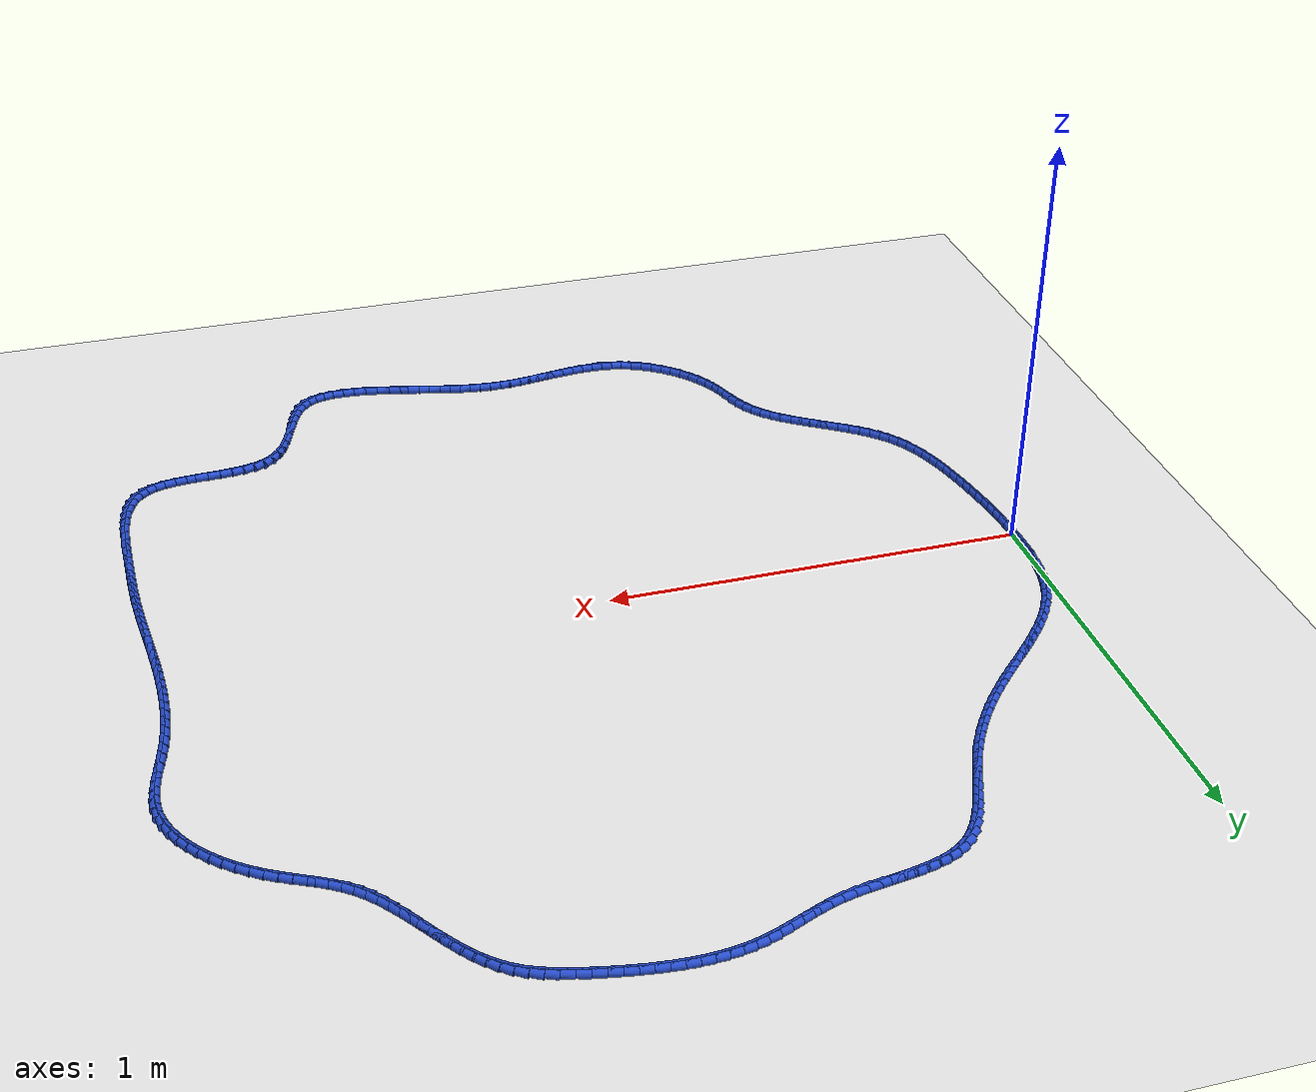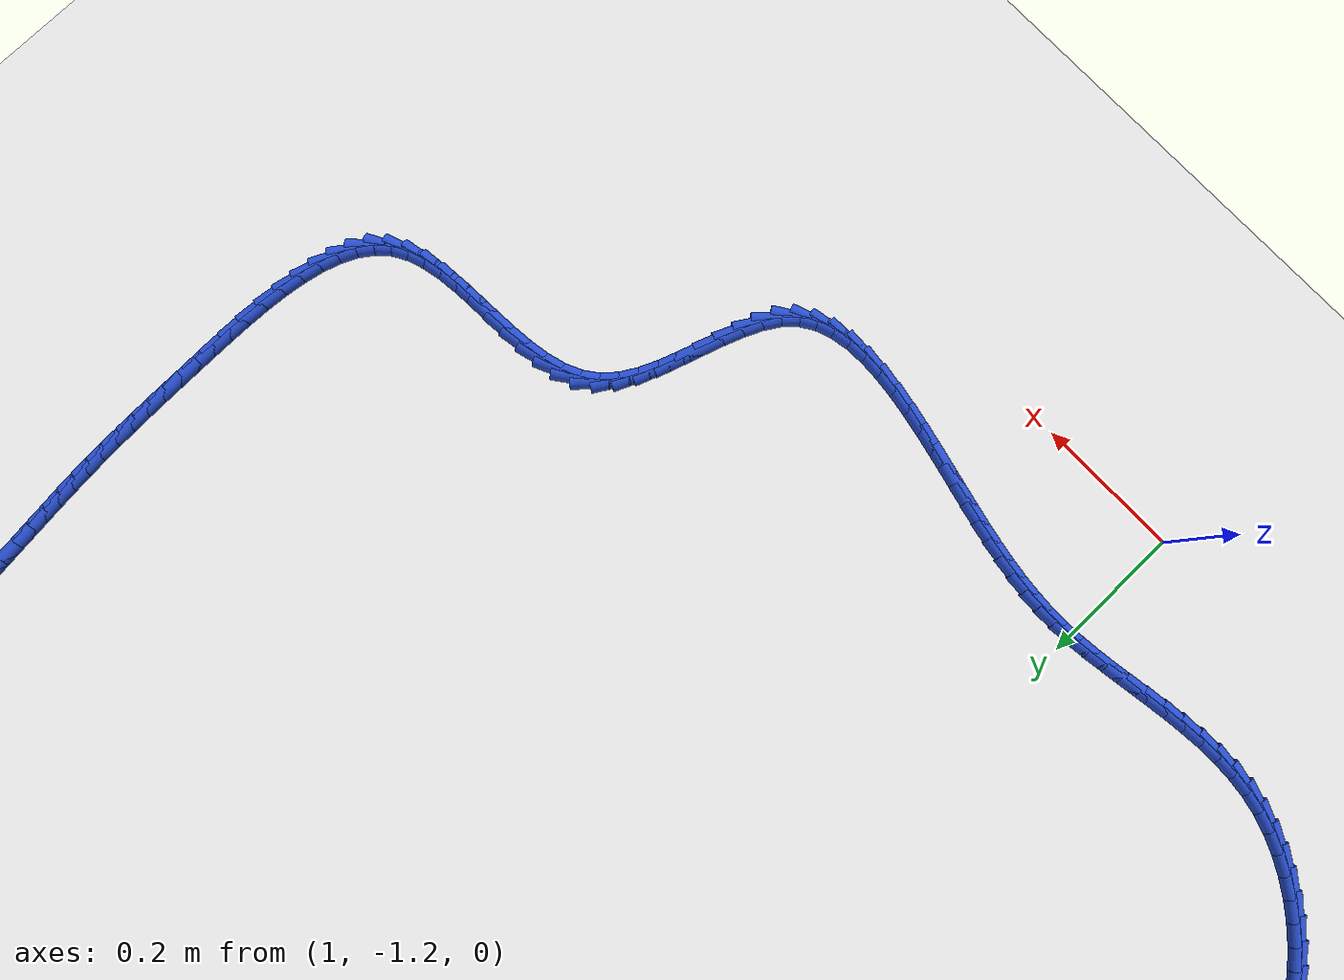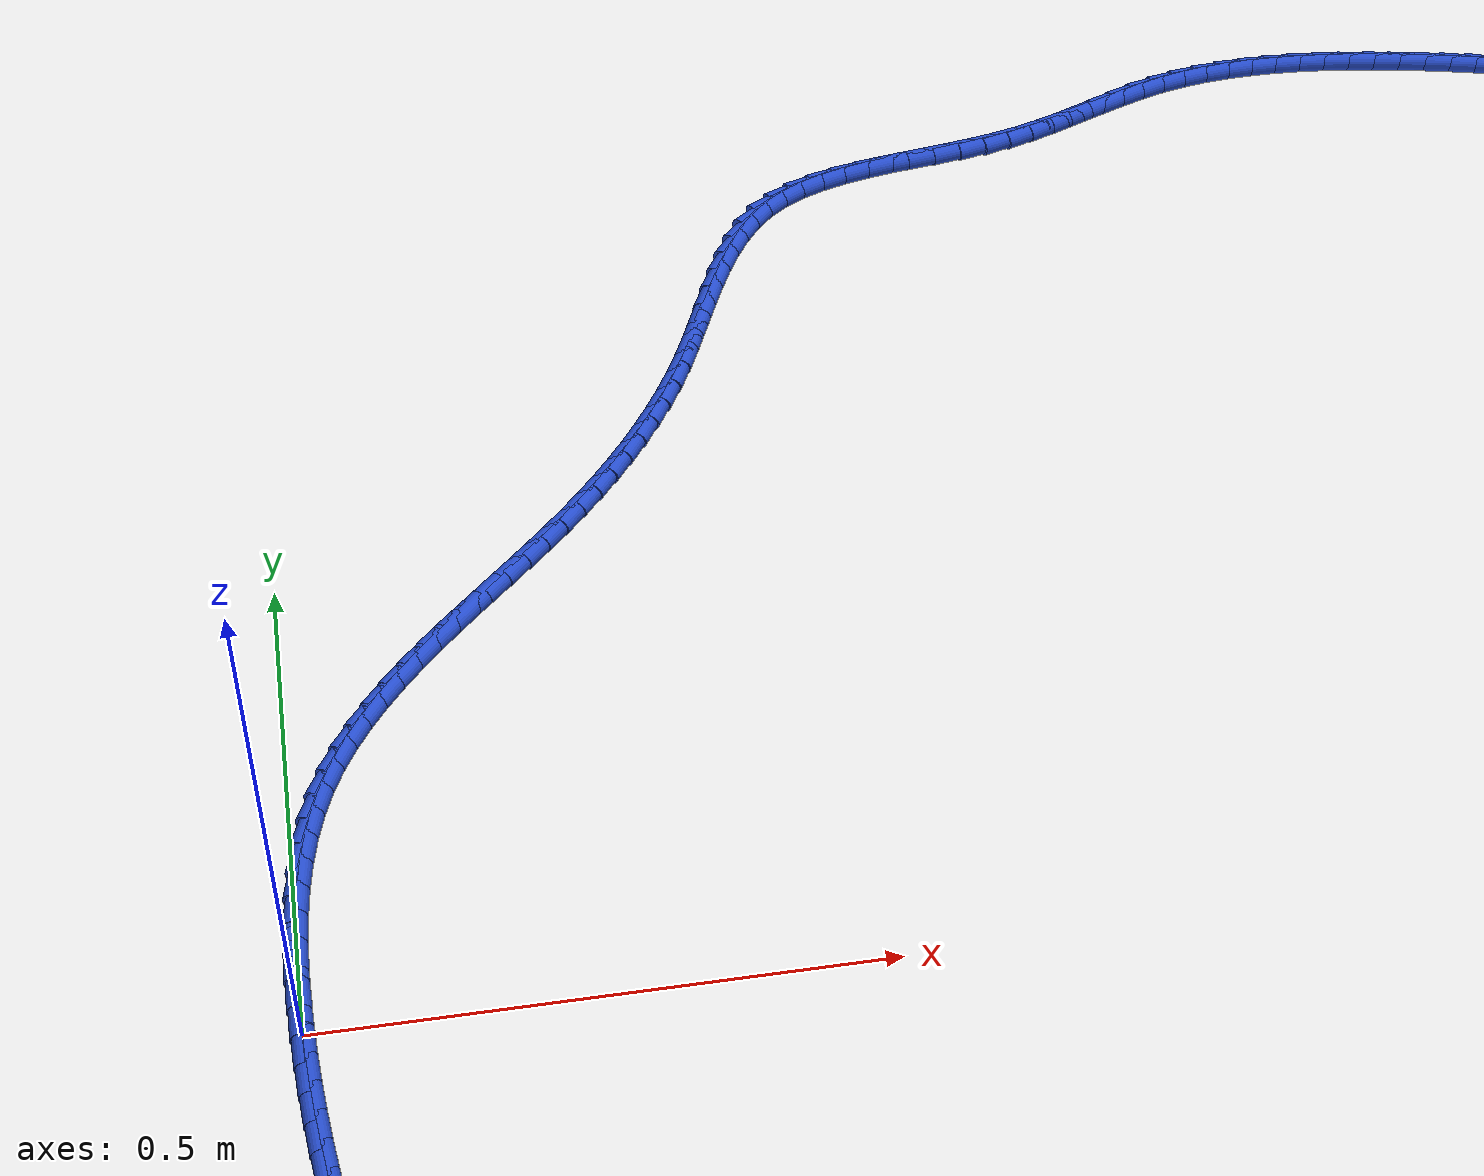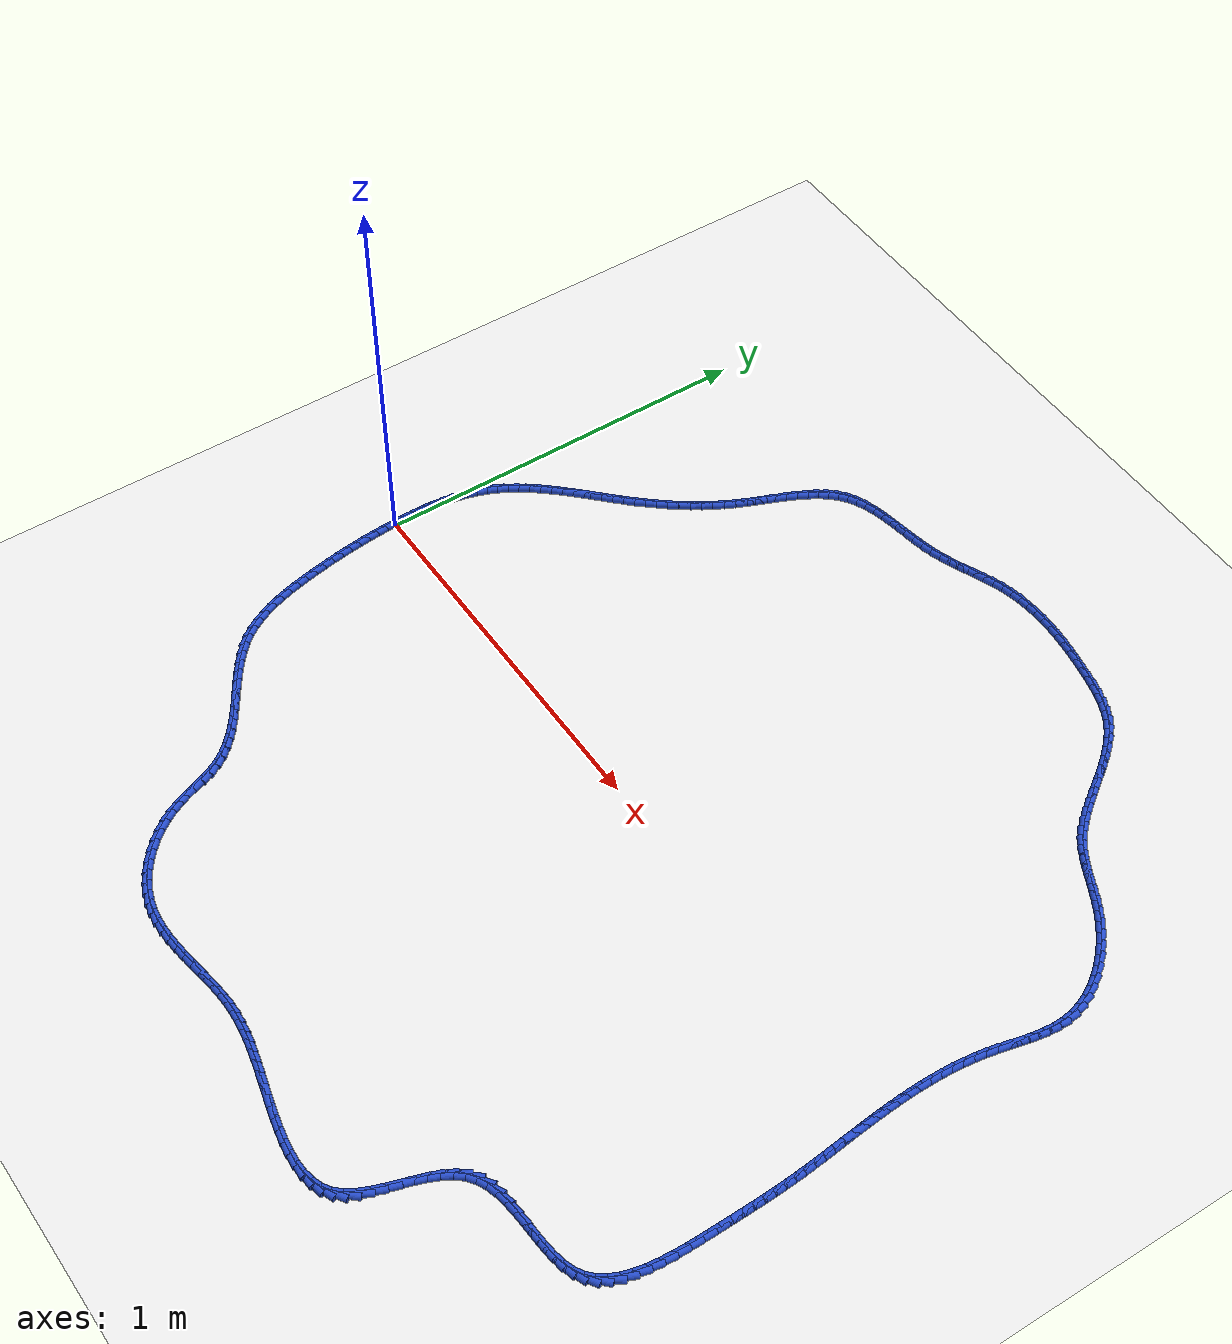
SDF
<sdf version="1.6">
 <world name="default">
  <light name="sun" type="directional">
   <pose>0 0 10 0 -0 0</pose>
   <diffuse>0.8 0.8 0.8 1</diffuse>
   <specular>0.2 0.2 0.2 1</specular>
   <attenuation>
    <range>1000</range>
    <constant>0.9</constant>
    <linear>0.01</linear>
    <quadratic>0.001</quadratic>
   </attenuation>
   <direction>-0.5 0.1 -0.9</direction>
  </light>
  <model name="ground_plane">
   <static>1</static>
   <link name="link">
    <collision name="collision">
     <geometry><plane><normal>0 0 1</normal><size>100 100</size></plane></geometry>
     <surface><friction><ode><mu>100</mu><mu2>50</mu2></ode></friction></surface>
    </collision>
    <visual name="visual">
     <cast_shadows>0</cast_shadows>
     <geometry><plane><normal>0 0 1</normal><size>100 100</size></plane></geometry>
     <material>
      <script><uri>file://media/materials/scripts/gazebo.material</uri><name>Gazebo/WhiteGlow</name></script>
     </material>
    </visual>
   </link>
  </model>
  <gravity>0 0 -9.8</gravity>
  <magnetic_field>6e-06 2.3e-05 -4.2e-05</magnetic_field>
  <atmosphere type="adiabatic"/>
  <physics name="default_physics" default="0" type="ode">
   <max_step_size>0.001</max_step_size>
   <real_time_factor>1</real_time_factor>
   <real_time_update_rate>1000</real_time_update_rate>
  </physics>
  <scene><ambient>0.4 0.4 0.4 1</ambient><background>0.7 0.7 0.7 1</background><shadows>1</shadows></scene>
  <spherical_coordinates>
   <surface_model>EARTH_WGS84</surface_model>
   <latitude_deg>0</latitude_deg>
   <longitude_deg>0</longitude_deg>
   <elevation>0</elevation>
   <heading_deg>0</heading_deg>
  </spherical_coordinates>
  <model name="line">
   <link name="link_0">
    <pose>1.0733601507606494e-17 -3.469446951953614e-17 0.01 0 1.57 -1.5398319304668007</pose>
    <collision name="collision">
     <geometry><cylinder><radius>0.01</radius><length>0.08</length></cylinder></geometry>
    </collision>
    <visual name="visual">
     <material>
      <script><name>Gazebo/Blue</name><uri>file://media/materials/scripts/gazebo.material</uri></script>
     </material>
     <geometry><cylinder><radius>0.01</radius><length>0.08</length></cylinder></geometry>
    </visual>
   </link>
   <link name="link_1">
    <pose>-0.0008739629196933045 0.028215747396649095 0.01 0 1.57 -1.5648753969789717</pose>
    <collision name="collision">
     <geometry><cylinder><radius>0.01</radius><length>0.08</length></cylinder></geometry>
    </collision>
    <visual name="visual">
     <material>
      <script><name>Gazebo/Blue</name><uri>file://media/materials/scripts/gazebo.material</uri></script>
     </material>
     <geometry><cylinder><radius>0.01</radius><length>0.08</length></cylinder></geometry>
    </visual>
   </link>
   <link name="link_2">
    <pose>-0.0010419331608630842 0.05658431171339357 0.01 0 1.57 1.546193624552556</pose>
    <collision name="collision">
     <geometry><cylinder><radius>0.01</radius><length>0.08</length></cylinder></geometry>
    </collision>
    <visual name="visual">
     <material>
      <script><name>Gazebo/Blue</name><uri>file://media/materials/scripts/gazebo.material</uri></script>
     </material>
     <geometry><cylinder><radius>0.01</radius><length>0.08</length></cylinder></geometry>
    </visual>
   </link>
   <link name="link_3">
    <pose>-0.0003435202010921314 0.08496623628374617 0.01 0 1.57 1.509816067381193</pose>
    <collision name="collision">
     <geometry><cylinder><radius>0.01</radius><length>0.08</length></cylinder></geometry>
    </collision>
    <visual name="visual">
     <material>
      <script><name>Gazebo/Blue</name><uri>file://media/materials/scripts/gazebo.material</uri></script>
     </material>
     <geometry><cylinder><radius>0.01</radius><length>0.08</length></cylinder></geometry>
    </visual>
   </link>
   <link name="link_4">
    <pose>0.0013816664820367492 0.11322206444121961 0.01 0 1.57 1.4671207166161329</pose>
    <collision name="collision">
     <geometry><cylinder><radius>0.01</radius><length>0.08</length></cylinder></geometry>
    </collision>
    <visual name="visual">
     <material>
      <script><name>Gazebo/Blue</name><uri>file://media/materials/scripts/gazebo.material</uri></script>
     </material>
     <geometry><cylinder><radius>0.01</radius><length>0.08</length></cylinder></geometry>
    </visual>
   </link>
   <link name="link_5">
    <pose>0.0042940174109407534 0.14121233951932657 0.01 0 1.57 1.417579775993468</pose>
    <collision name="collision">
     <geometry><cylinder><radius>0.01</radius><length>0.08</length></cylinder></geometry>
    </collision>
    <visual name="visual">
     <material>
      <script><name>Gazebo/Blue</name><uri>file://media/materials/scripts/gazebo.material</uri></script>
     </material>
     <geometry><cylinder><radius>0.01</radius><length>0.08</length></cylinder></geometry>
    </visual>
   </link>
   <link name="link_6">
    <pose>0.008553923108037079 0.16879760485157969 0.01 0 1.57 1.3606439043864245</pose>
    <collision name="collision">
     <geometry><cylinder><radius>0.01</radius><length>0.08</length></cylinder></geometry>
    </collision>
    <visual name="visual">
     <material>
      <script><name>Gazebo/Blue</name><uri>file://media/materials/scripts/gazebo.material</uri></script>
     </material>
     <geometry><cylinder><radius>0.01</radius><length>0.08</length></cylinder></geometry>
    </visual>
   </link>
   <link name="link_7">
    <pose>0.014321774095742925 0.19583840377149192 0.01 0 1.57 1.29580930253947</pose>
    <collision name="collision">
     <geometry><cylinder><radius>0.01</radius><length>0.08</length></cylinder></geometry>
    </collision>
    <visual name="visual">
     <material>
      <script><name>Gazebo/Blue</name><uri>file://media/materials/scripts/gazebo.material</uri></script>
     </material>
     <geometry><cylinder><radius>0.01</radius><length>0.08</length></cylinder></geometry>
    </visual>
   </link>
   <link name="link_8">
    <pose>0.02175796089647548 0.22219527961257562 0.01 0 1.57 1.2227171143530922</pose>
    <collision name="collision">
     <geometry><cylinder><radius>0.01</radius><length>0.08</length></cylinder></geometry>
    </collision>
    <visual name="visual">
     <material>
      <script><name>Gazebo/Blue</name><uri>file://media/materials/scripts/gazebo.material</uri></script>
     </material>
     <geometry><cylinder><radius>0.01</radius><length>0.08</length></cylinder></geometry>
    </visual>
   </link>
   <link name="link_9">
    <pose>0.031022874032651956 0.24772877570834376 0.01 0 1.57 1.143598132794401</pose>
    <collision name="collision">
     <geometry><cylinder><radius>0.01</radius><length>0.08</length></cylinder></geometry>
    </collision>
    <visual name="visual">
     <material>
      <script><name>Gazebo/Blue</name><uri>file://media/materials/scripts/gazebo.material</uri></script>
     </material>
     <geometry><cylinder><radius>0.01</radius><length>0.08</length></cylinder></geometry>
    </visual>
   </link>
   <link name="link_10">
    <pose>0.042223870284687666 0.2723336825484043 0.01 0 1.57 1.0693211557842757</pose>
    <collision name="collision">
     <geometry><cylinder><radius>0.01</radius><length>0.08</length></cylinder></geometry>
    </collision>
    <visual name="visual">
     <material>
      <script><name>Gazebo/Blue</name><uri>file://media/materials/scripts/gazebo.material</uri></script>
     </material>
     <geometry><cylinder><radius>0.01</radius><length>0.08</length></cylinder></geometry>
    </visual>
   </link>
   <link name="link_11">
    <pose>0.05523027740338111 0.29605850063838207 0.01 0 1.57 1.0034918648156992</pose>
    <collision name="collision">
     <geometry><cylinder><radius>0.01</radius><length>0.08</length></cylinder></geometry>
    </collision>
    <visual name="visual">
     <material>
      <script><name>Gazebo/Blue</name><uri>file://media/materials/scripts/gazebo.material</uri></script>
     </material>
     <geometry><cylinder><radius>0.01</radius><length>0.08</length></cylinder></geometry>
    </visual>
   </link>
   <link name="link_12">
    <pose>0.06984467120085563 0.318994836325149 0.01 0 1.57 0.9464020074330822</pose>
    <collision name="collision">
     <geometry><cylinder><radius>0.01</radius><length>0.08</length></cylinder></geometry>
    </collision>
    <visual name="visual">
     <material>
      <script><name>Gazebo/Blue</name><uri>file://media/materials/scripts/gazebo.material</uri></script>
     </material>
     <geometry><cylinder><radius>0.01</radius><length>0.08</length></cylinder></geometry>
    </visual>
   </link>
   <link name="link_13">
    <pose>0.08586962412369734 0.3412342981289122 0.01 0 1.57 0.8980108743850942</pose>
    <collision name="collision">
     <geometry><cylinder><radius>0.01</radius><length>0.08</length></cylinder></geometry>
    </collision>
    <visual name="visual">
     <material>
      <script><name>Gazebo/Blue</name><uri>file://media/materials/scripts/gazebo.material</uri></script>
     </material>
     <geometry><cylinder><radius>0.01</radius><length>0.08</length></cylinder></geometry>
    </visual>
   </link>
   <link name="link_14">
    <pose>0.10310770861849235 0.3628684945698781 0.01 0 1.57 0.8580775403388963</pose>
    <collision name="collision">
     <geometry><cylinder><radius>0.01</radius><length>0.08</length></cylinder></geometry>
    </collision>
    <visual name="visual">
     <material>
      <script><name>Gazebo/Blue</name><uri>file://media/materials/scripts/gazebo.material</uri></script>
     </material>
     <geometry><cylinder><radius>0.01</radius><length>0.08</length></cylinder></geometry>
    </visual>
   </link>
   <link name="link_15">
    <pose>0.12136149713182674 0.3839890341682537 0.01 0 1.57 0.8262706245816464</pose>
    <collision name="collision">
     <geometry><cylinder><radius>0.01</radius><length>0.08</length></cylinder></geometry>
    </collision>
    <visual name="visual">
     <material>
      <script><name>Gazebo/Blue</name><uri>file://media/materials/scripts/gazebo.material</uri></script>
     </material>
     <geometry><cylinder><radius>0.01</radius><length>0.08</length></cylinder></geometry>
    </visual>
   </link>
   <link name="link_16">
    <pose>0.14043356211028674 0.4046875254442459 0.01 0 1.57 0.8022493219237204</pose>
    <collision name="collision">
     <geometry><cylinder><radius>0.01</radius><length>0.08</length></cylinder></geometry>
    </collision>
    <visual name="visual">
     <material>
      <script><name>Gazebo/Blue</name><uri>file://media/materials/scripts/gazebo.material</uri></script>
     </material>
     <geometry><cylinder><radius>0.01</radius><length>0.08</length></cylinder></geometry>
    </visual>
   </link>
   <link name="link_17">
    <pose>0.1601264760004584 0.42505557691806156 0.01 0 1.57 0.785718321556414</pose>
    <collision name="collision">
     <geometry><cylinder><radius>0.01</radius><length>0.08</length></cylinder></geometry>
    </collision>
    <visual name="visual">
     <material>
      <script><name>Gazebo/Blue</name><uri>file://media/materials/scripts/gazebo.material</uri></script>
     </material>
     <geometry><cylinder><radius>0.01</radius><length>0.08</length></cylinder></geometry>
    </visual>
   </link>
   <link name="link_18">
    <pose>0.18024281124892788 0.4451847971099076 0.01 0 1.57 0.776462563861803</pose>
    <collision name="collision">
     <geometry><cylinder><radius>0.01</radius><length>0.08</length></cylinder></geometry>
    </collision>
    <visual name="visual">
     <material>
      <script><name>Gazebo/Blue</name><uri>file://media/materials/scripts/gazebo.material</uri></script>
     </material>
     <geometry><cylinder><radius>0.01</radius><length>0.08</length></cylinder></geometry>
    </visual>
   </link>
   <link name="link_19">
    <pose>0.2005851403022812 0.46516679453999044 0.01 0 1.57 0.7743677885194766</pose>
    <collision name="collision">
     <geometry><cylinder><radius>0.01</radius><length>0.08</length></cylinder></geometry>
    </collision>
    <visual name="visual">
     <material>
      <script><name>Gazebo/Blue</name><uri>file://media/materials/scripts/gazebo.material</uri></script>
     </material>
     <geometry><cylinder><radius>0.01</radius><length>0.08</length></cylinder></geometry>
    </visual>
   </link>
   <link name="link_20">
    <pose>0.22095603560710458 0.4850931777285172 0.01 0 1.57 0.7794313464376725</pose>
    <collision name="collision">
     <geometry><cylinder><radius>0.01</radius><length>0.08</length></cylinder></geometry>
    </collision>
    <visual name="visual">
     <material>
      <script><name>Gazebo/Blue</name><uri>file://media/materials/scripts/gazebo.material</uri></script>
     </material>
     <geometry><cylinder><radius>0.01</radius><length>0.08</length></cylinder></geometry>
    </visual>
   </link>
   <link name="link_21">
    <pose>0.24115806960998415 0.5050555551956948 0.01 0 1.57 0.7917657792579809</pose>
    <collision name="collision">
     <geometry><cylinder><radius>0.01</radius><length>0.08</length></cylinder></geometry>
    </collision>
    <visual name="visual">
     <material>
      <script><name>Gazebo/Blue</name><uri>file://media/materials/scripts/gazebo.material</uri></script>
     </material>
     <geometry><cylinder><radius>0.01</radius><length>0.08</length></cylinder></geometry>
    </visual>
   </link>
   <link name="link_22">
    <pose>0.26099381475750594 0.5251455354617299 0.01 0 1.57 0.8114603091971061</pose>
    <collision name="collision">
     <geometry><cylinder><radius>0.01</radius><length>0.08</length></cylinder></geometry>
    </collision>
    <visual name="visual">
     <material>
      <script><name>Gazebo/Blue</name><uri>file://media/materials/scripts/gazebo.material</uri></script>
     </material>
     <geometry><cylinder><radius>0.01</radius><length>0.08</length></cylinder></geometry>
    </visual>
   </link>
   <link name="link_23">
    <pose>0.2802706182837798 0.5454542563455986 0.01 0 1.57 0.8361251301242908</pose>
    <collision name="collision">
     <geometry><cylinder><radius>0.01</radius><length>0.08</length></cylinder></geometry>
    </collision>
    <visual name="visual">
     <material>
      <script><name>Gazebo/Blue</name><uri>file://media/materials/scripts/gazebo.material</uri></script>
     </material>
     <geometry><cylinder><radius>0.01</radius><length>0.08</length></cylinder></geometry>
    </visual>
   </link>
   <link name="link_24">
    <pose>0.29888849046054056 0.5660637208920856 0.01 0 1.57 0.863359270496928</pose>
    <collision name="collision">
     <geometry><cylinder><radius>0.01</radius><length>0.08</length></cylinder></geometry>
    </collision>
    <visual name="visual">
     <material>
      <script><name>Gazebo/Blue</name><uri>file://media/materials/scripts/gazebo.material</uri></script>
     </material>
     <geometry><cylinder><radius>0.01</radius><length>0.08</length></cylinder></geometry>
    </visual>
   </link>
   <link name="link_25">
    <pose>0.3168314699730497 0.5870476485778667 0.01 0 1.57 0.8929415308446829</pose>
    <collision name="collision">
     <geometry><cylinder><radius>0.01</radius><length>0.08</length></cylinder></geometry>
    </collision>
    <visual name="visual">
     <material>
      <script><name>Gazebo/Blue</name><uri>file://media/materials/scripts/gazebo.material</uri></script>
     </material>
     <geometry><cylinder><radius>0.01</radius><length>0.08</length></cylinder></geometry>
    </visual>
   </link>
   <link name="link_26">
    <pose>0.33408663818808526 0.6084794589303689 0.01 0 1.57 0.9246881062299116</pose>
    <collision name="collision">
     <geometry><cylinder><radius>0.01</radius><length>0.08</length></cylinder></geometry>
    </collision>
    <visual name="visual">
     <material>
      <script><name>Gazebo/Blue</name><uri>file://media/materials/scripts/gazebo.material</uri></script>
     </material>
     <geometry><cylinder><radius>0.01</radius><length>0.08</length></cylinder></geometry>
    </visual>
   </link>
   <link name="link_27">
    <pose>0.3506410764724255 0.6304325714770184 0.01 0 1.57 0.9583666812969304</pose>
    <collision name="collision">
     <geometry><cylinder><radius>0.01</radius><length>0.08</length></cylinder></geometry>
    </collision>
    <visual name="visual">
     <material>
      <script><name>Gazebo/Blue</name><uri>file://media/materials/scripts/gazebo.material</uri></script>
     </material>
     <geometry><cylinder><radius>0.01</radius><length>0.08</length></cylinder></geometry>
    </visual>
   </link>
   <link name="link_28">
    <pose>0.36648186619284834 0.6529804057452422 0.01 0 1.57 0.9936996088033377</pose>
    <collision name="collision">
     <geometry><cylinder><radius>0.01</radius><length>0.08</length></cylinder></geometry>
    </collision>
    <visual name="visual">
     <material>
      <script><name>Gazebo/Blue</name><uri>file://media/materials/scripts/gazebo.material</uri></script>
     </material>
     <geometry><cylinder><radius>0.01</radius><length>0.08</length></cylinder></geometry>
    </visual>
   </link>
   <link name="link_29">
    <pose>0.38159608871613215 0.6761963812624668 0.01 0 1.57 1.030370230421064</pose>
    <collision name="collision">
     <geometry><cylinder><radius>0.01</radius><length>0.08</length></cylinder></geometry>
    </collision>
    <visual name="visual">
     <material>
      <script><name>Gazebo/Blue</name><uri>file://media/materials/scripts/gazebo.material</uri></script>
     </material>
     <geometry><cylinder><radius>0.01</radius><length>0.08</length></cylinder></geometry>
    </visual>
   </link>
   <link name="link_30">
    <pose>0.3959708254090549 0.7001539175561191 0.01 0 1.57 1.0680322082319915</pose>
    <collision name="collision">
     <geometry><cylinder><radius>0.01</radius><length>0.08</length></cylinder></geometry>
    </collision>
    <visual name="visual">
     <material>
      <script><name>Gazebo/Blue</name><uri>file://media/materials/scripts/gazebo.material</uri></script>
     </material>
     <geometry><cylinder><radius>0.01</radius><length>0.08</length></cylinder></geometry>
    </visual>
   </link>
   <link name="link_31">
    <pose>0.40959315763839477 0.7249264341536255 0.01 0 1.57 1.1063213138940085</pose>
    <collision name="collision">
     <geometry><cylinder><radius>0.01</radius><length>0.08</length></cylinder></geometry>
    </collision>
    <visual name="visual">
     <material>
      <script><name>Gazebo/Blue</name><uri>file://media/materials/scripts/gazebo.material</uri></script>
     </material>
     <geometry><cylinder><radius>0.01</radius><length>0.08</length></cylinder></geometry>
    </visual>
   </link>
   <link name="link_32">
    <pose>0.42245016677093 0.7505873505824128 0.01 0 1.57 1.1424172319542438</pose>
    <collision name="collision">
     <geometry><cylinder><radius>0.01</radius><length>0.08</length></cylinder></geometry>
    </collision>
    <visual name="visual">
     <material>
      <script><name>Gazebo/Blue</name><uri>file://media/materials/scripts/gazebo.material</uri></script>
     </material>
     <geometry><cylinder><radius>0.01</radius><length>0.08</length></cylinder></geometry>
    </visual>
   </link>
   <link name="link_33">
    <pose>0.43457579925530965 0.7771401806810869 0.01 0 1.57 1.164592994442675</pose>
    <collision name="collision">
     <geometry><cylinder><radius>0.01</radius><length>0.08</length></cylinder></geometry>
    </collision>
    <visual name="visual">
     <material>
      <script><name>Gazebo/Blue</name><uri>file://media/materials/scripts/gazebo.material</uri></script>
     </material>
     <geometry><cylinder><radius>0.01</radius><length>0.08</length></cylinder></geometry>
    </visual>
   </link>
   <link name="link_34">
    <pose>0.44623424936177686 0.8042449921248135 0.01 0 1.57 1.170135821235586</pose>
    <collision name="collision">
     <geometry><cylinder><radius>0.01</radius><length>0.08</length></cylinder></geometry>
    </collision>
    <visual name="visual">
     <material>
      <script><name>Gazebo/Blue</name><uri>file://media/materials/scripts/gazebo.material</uri></script>
     </material>
     <geometry><cylinder><radius>0.01</radius><length>0.08</length></cylinder></geometry>
    </visual>
   </link>
   <link name="link_35">
    <pose>0.4577603048082262 0.8314565527922518 0.01 0 1.57 1.1592761554816913</pose>
    <collision name="collision">
     <geometry><cylinder><radius>0.01</radius><length>0.08</length></cylinder></geometry>
    </collision>
    <visual name="visual">
     <material>
      <script><name>Gazebo/Blue</name><uri>file://media/materials/scripts/gazebo.material</uri></script>
     </material>
     <geometry><cylinder><radius>0.01</radius><length>0.08</length></cylinder></geometry>
    </visual>
   </link>
   <link name="link_36">
    <pose>0.4694887718142246 0.8583296029642821 0.01 0 1.57 1.131318556628179</pose>
    <collision name="collision">
     <geometry><cylinder><radius>0.01</radius><length>0.08</length></cylinder></geometry>
    </collision>
    <visual name="visual">
     <material>
      <script><name>Gazebo/Blue</name><uri>file://media/materials/scripts/gazebo.material</uri></script>
     </material>
     <geometry><cylinder><radius>0.01</radius><length>0.08</length></cylinder></geometry>
    </visual>
   </link>
   <link name="link_37">
    <pose>0.48175445659933874 0.8844188829217849 0.01 0 1.57 1.0846388731227439</pose>
    <collision name="collision">
     <geometry><cylinder><radius>0.01</radius><length>0.08</length></cylinder></geometry>
    </collision>
    <visual name="visual">
     <material>
      <script><name>Gazebo/Blue</name><uri>file://media/materials/scripts/gazebo.material</uri></script>
     </material>
     <geometry><cylinder><radius>0.01</radius><length>0.08</length></cylinder></geometry>
    </visual>
   </link>
   <link name="link_38">
    <pose>0.49489216538313535 0.9092791329456409 0.01 0 1.57 1.0167593533997539</pose>
    <collision name="collision">
     <geometry><cylinder><radius>0.01</radius><length>0.08</length></cylinder></geometry>
    </collision>
    <visual name="visual">
     <material>
      <script><name>Gazebo/Blue</name><uri>file://media/materials/scripts/gazebo.material</uri></script>
     </material>
     <geometry><cylinder><radius>0.01</radius><length>0.08</length></cylinder></geometry>
    </visual>
   </link>
   <link name="link_39">
    <pose>0.5092367043851812 0.9324650933167309 0.01 0 1.57 0.9246765320449766</pose>
    <collision name="collision">
     <geometry><cylinder><radius>0.01</radius><length>0.08</length></cylinder></geometry>
    </collision>
    <visual name="visual">
     <material>
      <script><name>Gazebo/Blue</name><uri>file://media/materials/scripts/gazebo.material</uri></script>
     </material>
     <geometry><cylinder><radius>0.01</radius><length>0.08</length></cylinder></geometry>
    </visual>
   </link>
   <link name="link_40">
    <pose>0.5251228798250435 0.9535315043159357 0.01 0 1.57 0.8057731100477616</pose>
    <collision name="collision">
     <geometry><cylinder><radius>0.01</radius><length>0.08</length></cylinder></geometry>
    </collision>
    <visual name="visual">
     <material>
      <script><name>Gazebo/Blue</name><uri>file://media/materials/scripts/gazebo.material</uri></script>
     </material>
     <geometry><cylinder><radius>0.01</radius><length>0.08</length></cylinder></geometry>
    </visual>
   </link>
   <link name="link_41">
    <pose>0.5428854979222884 0.9720331062241352 0.01 0 1.57 0.6602333291594917</pose>
    <collision name="collision">
     <geometry><cylinder><radius>0.01</radius><length>0.08</length></cylinder></geometry>
    </collision>
    <visual name="visual">
     <material>
      <script><name>Gazebo/Blue</name><uri>file://media/materials/scripts/gazebo.material</uri></script>
     </material>
     <geometry><cylinder><radius>0.01</radius><length>0.08</length></cylinder></geometry>
    </visual>
   </link>
   <link name="link_42">
    <pose>0.5628512656900937 0.987536102678552 0.01 0 1.57 0.5114736847651868</pose>
    <collision name="collision">
     <geometry><cylinder><radius>0.01</radius><length>0.08</length></cylinder></geometry>
    </collision>
    <visual name="visual">
     <material>
      <script><name>Gazebo/Blue</name><uri>file://media/materials/scripts/gazebo.material</uri></script>
     </material>
     <geometry><cylinder><radius>0.01</radius><length>0.08</length></cylinder></geometry>
    </visual>
   </link>
   <link name="link_43">
    <pose>0.5850655630370231 1.0000048786558762 0.01 0 1.57 0.3885397376110385</pose>
    <collision name="collision">
     <geometry><cylinder><radius>0.01</radius><length>0.08</length></cylinder></geometry>
    </collision>
    <visual name="visual">
     <material>
      <script><name>Gazebo/Blue</name><uri>file://media/materials/scripts/gazebo.material</uri></script>
     </material>
     <geometry><cylinder><radius>0.01</radius><length>0.08</length></cylinder></geometry>
    </visual>
   </link>
   <link name="link_44">
    <pose>0.6092266102296122 1.0098951777292653 0.01 0 1.57 0.2936809650711544</pose>
    <collision name="collision">
     <geometry><cylinder><radius>0.01</radius><length>0.08</length></cylinder></geometry>
    </collision>
    <visual name="visual">
     <material>
      <script><name>Gazebo/Blue</name><uri>file://media/materials/scripts/gazebo.material</uri></script>
     </material>
     <geometry><cylinder><radius>0.01</radius><length>0.08</length></cylinder></geometry>
    </visual>
   </link>
   <link name="link_45">
    <pose>0.6350111790706325 1.0176931009379429 0.01 0 1.57 0.2247400355590737</pose>
    <collision name="collision">
     <geometry><cylinder><radius>0.01</radius><length>0.08</length></cylinder></geometry>
    </collision>
    <visual name="visual">
     <material>
      <script><name>Gazebo/Blue</name><uri>file://media/materials/scripts/gazebo.material</uri></script>
     </material>
     <geometry><cylinder><radius>0.01</radius><length>0.08</length></cylinder></geometry>
    </visual>
   </link>
   <link name="link_46">
    <pose>0.6620960413628557 1.0238847493211305 0.01 0 1.57 0.17879450097534663</pose>
    <collision name="collision">
     <geometry><cylinder><radius>0.01</radius><length>0.08</length></cylinder></geometry>
    </collision>
    <visual name="visual">
     <material>
      <script><name>Gazebo/Blue</name><uri>file://media/materials/scripts/gazebo.material</uri></script>
     </material>
     <geometry><cylinder><radius>0.01</radius><length>0.08</length></cylinder></geometry>
    </visual>
   </link>
   <link name="link_47">
    <pose>0.6901579689090529 1.0289562239180507 0.01 0 1.57 0.15331575514629203</pose>
    <collision name="collision">
     <geometry><cylinder><radius>0.01</radius><length>0.08</length></cylinder></geometry>
    </collision>
    <visual name="visual">
     <material>
      <script><name>Gazebo/Blue</name><uri>file://media/materials/scripts/gazebo.material</uri></script>
     </material>
     <geometry><cylinder><radius>0.01</radius><length>0.08</length></cylinder></geometry>
    </visual>
   </link>
   <link name="link_48">
    <pose>0.718873733511996 1.0333936257679266 0.01 0 1.57 0.14661557094771469</pose>
    <collision name="collision">
     <geometry><cylinder><radius>0.01</radius><length>0.08</length></cylinder></geometry>
    </collision>
    <visual name="visual">
     <material>
      <script><name>Gazebo/Blue</name><uri>file://media/materials/scripts/gazebo.material</uri></script>
     </material>
     <geometry><cylinder><radius>0.01</radius><length>0.08</length></cylinder></geometry>
    </visual>
   </link>
   <link name="link_49">
    <pose>0.7479201069744563 1.0376830559099797 0.01 0 1.57 0.15794904390612338</pose>
    <collision name="collision">
     <geometry><cylinder><radius>0.01</radius><length>0.08</length></cylinder></geometry>
    </collision>
    <visual name="visual">
     <material>
      <script><name>Gazebo/Blue</name><uri>file://media/materials/scripts/gazebo.material</uri></script>
     </material>
     <geometry><cylinder><radius>0.01</radius><length>0.08</length></cylinder></geometry>
    </visual>
   </link>
   <link name="link_50">
    <pose>0.7769738610992054 1.042310615383433 0.01 0 1.57 0.18747940203370997</pose>
    <collision name="collision">
     <geometry><cylinder><radius>0.01</radius><length>0.08</length></cylinder></geometry>
    </collision>
    <visual name="visual">
     <material>
      <script><name>Gazebo/Blue</name><uri>file://media/materials/scripts/gazebo.material</uri></script>
     </material>
     <geometry><cylinder><radius>0.01</radius><length>0.08</length></cylinder></geometry>
    </visual>
   </link>
   <link name="link_51">
    <pose>0.8057117676890144 1.0477624052275085 0.01 0 1.57 0.23616333381526736</pose>
    <collision name="collision">
     <geometry><cylinder><radius>0.01</radius><length>0.08</length></cylinder></geometry>
    </collision>
    <visual name="visual">
     <material>
      <script><name>Gazebo/Blue</name><uri>file://media/materials/scripts/gazebo.material</uri></script>
     </material>
     <geometry><cylinder><radius>0.01</radius><length>0.08</length></cylinder></geometry>
    </visual>
   </link>
   <link name="link_52">
    <pose>0.8338106094629603 1.0545245057891517 0.01 0 1.57 0.29800604289535454</pose>
    <collision name="collision">
     <geometry><cylinder><radius>0.01</radius><length>0.08</length></cylinder></geometry>
    </collision>
    <visual name="visual">
     <material>
      <script><name>Gazebo/Blue</name><uri>file://media/materials/scripts/gazebo.material</uri></script>
     </material>
     <geometry><cylinder><radius>0.01</radius><length>0.08</length></cylinder></geometry>
    </visual>
   </link>
   <link name="link_53">
    <pose>0.8610485997523967 1.062890731774053 0.01 0 1.57 0.3475621143609681</pose>
    <collision name="collision">
     <geometry><cylinder><radius>0.01</radius><length>0.08</length></cylinder></geometry>
    </collision>
    <visual name="visual">
     <material>
      <script><name>Gazebo/Blue</name><uri>file://media/materials/scripts/gazebo.material</uri></script>
     </material>
     <geometry><cylinder><radius>0.01</radius><length>0.08</length></cylinder></geometry>
    </visual>
   </link>
   <link name="link_54">
    <pose>0.8875533676087901 1.072492566901402 0.01 0 1.57 0.37840269732567994</pose>
    <collision name="collision">
     <geometry><cylinder><radius>0.01</radius><length>0.08</length></cylinder></geometry>
    </collision>
    <visual name="visual">
     <material>
      <script><name>Gazebo/Blue</name><uri>file://media/materials/scripts/gazebo.material</uri></script>
     </material>
     <geometry><cylinder><radius>0.01</radius><length>0.08</length></cylinder></geometry>
    </visual>
   </link>
   <link name="link_55">
    <pose>0.9135277267973817 1.0828189793629523 0.01 0 1.57 0.38992426332164404</pose>
    <collision name="collision">
     <geometry><cylinder><radius>0.01</radius><length>0.08</length></cylinder></geometry>
    </collision>
    <visual name="visual">
     <material>
      <script><name>Gazebo/Blue</name><uri>file://media/materials/scripts/gazebo.material</uri></script>
     </material>
     <geometry><cylinder><radius>0.01</radius><length>0.08</length></cylinder></geometry>
    </visual>
   </link>
   <link name="link_56">
    <pose>0.9391744910834139 1.0933589373504589 0.01 0 1.57 0.3816434331658473</pose>
    <collision name="collision">
     <geometry><cylinder><radius>0.01</radius><length>0.08</length></cylinder></geometry>
    </collision>
    <visual name="visual">
     <material>
      <script><name>Gazebo/Blue</name><uri>file://media/materials/scripts/gazebo.material</uri></script>
     </material>
     <geometry><cylinder><radius>0.01</radius><length>0.08</length></cylinder></geometry>
    </visual>
   </link>
   <link name="link_57">
    <pose>0.9646964742321287 1.1036014090556772 0.01 0 1.57 0.35307185985536405</pose>
    <collision name="collision">
     <geometry><cylinder><radius>0.01</radius><length>0.08</length></cylinder></geometry>
    </collision>
    <visual name="visual">
     <material>
      <script><name>Gazebo/Blue</name><uri>file://media/materials/scripts/gazebo.material</uri></script>
     </material>
     <geometry><cylinder><radius>0.01</radius><length>0.08</length></cylinder></geometry>
    </visual>
   </link>
   <link name="link_58">
    <pose>0.9902964900087675 1.113035362670361 0.01 0 1.57 0.30382214685115905</pose>
    <collision name="collision">
     <geometry><cylinder><radius>0.01</radius><length>0.08</length></cylinder></geometry>
    </collision>
    <visual name="visual">
     <material>
      <script><name>Gazebo/Blue</name><uri>file://media/materials/scripts/gazebo.material</uri></script>
     </material>
     <geometry><cylinder><radius>0.01</radius><length>0.08</length></cylinder></geometry>
    </visual>
   </link>
   <link name="link_59">
    <pose>1.016177352178573 1.121149766386266 0.01 0 1.57 0.2371604154753137</pose>
    <collision name="collision">
     <geometry><cylinder><radius>0.01</radius><length>0.08</length></cylinder></geometry>
    </collision>
    <visual name="visual">
     <material>
      <script><name>Gazebo/Blue</name><uri>file://media/materials/scripts/gazebo.material</uri></script>
     </material>
     <geometry><cylinder><radius>0.01</radius><length>0.08</length></cylinder></geometry>
    </visual>
   </link>
   <link name="link_60">
    <pose>1.0425087250473066 1.127514300086119 0.01 0 1.57 0.17025556475605913</pose>
    <collision name="collision">
     <geometry><cylinder><radius>0.01</radius><length>0.08</length></cylinder></geometry>
    </collision>
    <visual name="visual">
     <material>
      <script><name>Gazebo/Blue</name><uri>file://media/materials/scripts/gazebo.material</uri></script>
     </material>
     <geometry><cylinder><radius>0.01</radius><length>0.08</length></cylinder></geometry>
    </visual>
   </link>
   <link name="link_61">
    <pose>1.0692879614228532 1.1321181845014565 0.01 0 1.57 0.10882468767725949</pose>
    <collision name="collision">
     <geometry><cylinder><radius>0.01</radius><length>0.08</length></cylinder></geometry>
    </collision>
    <visual name="visual">
     <material>
      <script><name>Gazebo/Blue</name><uri>file://media/materials/scripts/gazebo.material</uri></script>
     </material>
     <geometry><cylinder><radius>0.01</radius><length>0.08</length></cylinder></geometry>
    </visual>
   </link>
   <link name="link_62">
    <pose>1.096456602086862 1.1350865304532647 0.01 0 1.57 0.052969005391412013</pose>
    <collision name="collision">
     <geometry><cylinder><radius>0.01</radius><length>0.08</length></cylinder></geometry>
    </collision>
    <visual name="visual">
     <material>
      <script><name>Gazebo/Blue</name><uri>file://media/materials/scripts/gazebo.material</uri></script>
     </material>
     <geometry><cylinder><radius>0.01</radius><length>0.08</length></cylinder></geometry>
    </visual>
   </link>
   <link name="link_63">
    <pose>1.1239561591937555 1.1365445184635767 0.01 0 1.57 0.002621721932465468</pose>
    <collision name="collision">
     <geometry><cylinder><radius>0.01</radius><length>0.08</length></cylinder></geometry>
    </collision>
    <visual name="visual">
     <material>
      <script><name>Gazebo/Blue</name><uri>file://media/materials/scripts/gazebo.material</uri></script>
     </material>
     <geometry><cylinder><radius>0.01</radius><length>0.08</length></cylinder></geometry>
    </visual>
   </link>
   <link name="link_64">
    <pose>1.1517281448979548 1.136617329054425 0.01 0 1.57 -0.042395414414124734</pose>
    <collision name="collision">
     <geometry><cylinder><radius>0.01</radius><length>0.08</length></cylinder></geometry>
    </collision>
    <visual name="visual">
     <material>
      <script><name>Gazebo/Blue</name><uri>file://media/materials/scripts/gazebo.material</uri></script>
     </material>
     <geometry><cylinder><radius>0.01</radius><length>0.08</length></cylinder></geometry>
    </visual>
   </link>
   <link name="link_65">
    <pose>1.1797140713538823 1.1354301427478426 0.01 0 1.57 -0.08232554958904123</pose>
    <collision name="collision">
     <geometry><cylinder><radius>0.01</radius><length>0.08</length></cylinder></geometry>
    </collision>
    <visual name="visual">
     <material>
      <script><name>Gazebo/Blue</name><uri>file://media/materials/scripts/gazebo.material</uri></script>
     </material>
     <geometry><cylinder><radius>0.01</radius><length>0.08</length></cylinder></geometry>
    </visual>
   </link>
   <link name="link_66">
    <pose>1.2078554507159593 1.1331081400658622 0.01 0 1.57 -0.11743987511740568</pose>
    <collision name="collision">
     <geometry><cylinder><radius>0.01</radius><length>0.08</length></cylinder></geometry>
    </collision>
    <visual name="visual">
     <material>
      <script><name>Gazebo/Blue</name><uri>file://media/materials/scripts/gazebo.material</uri></script>
     </material>
     <geometry><cylinder><radius>0.01</radius><length>0.08</length></cylinder></geometry>
    </visual>
   </link>
   <link name="link_67">
    <pose>1.2360937951386077 1.129776501530516 0.01 0 1.57 -0.14801031963670133</pose>
    <collision name="collision">
     <geometry><cylinder><radius>0.01</radius><length>0.08</length></cylinder></geometry>
    </collision>
    <visual name="visual">
     <material>
      <script><name>Gazebo/Blue</name><uri>file://media/materials/scripts/gazebo.material</uri></script>
     </material>
     <geometry><cylinder><radius>0.01</radius><length>0.08</length></cylinder></geometry>
    </visual>
   </link>
   <link name="link_68">
    <pose>1.2643706167762492 1.1255604076638377 0.01 0 1.57 -0.17429027165801564</pose>
    <collision name="collision">
     <geometry><cylinder><radius>0.01</radius><length>0.08</length></cylinder></geometry>
    </collision>
    <visual name="visual">
     <material>
      <script><name>Gazebo/Blue</name><uri>file://media/materials/scripts/gazebo.material</uri></script>
     </material>
     <geometry><cylinder><radius>0.01</radius><length>0.08</length></cylinder></geometry>
    </visual>
   </link>
   <link name="link_69">
    <pose>1.292627427783305 1.1205850389878593 0.01 0 1.57 -0.19650138399546405</pose>
    <collision name="collision">
     <geometry><cylinder><radius>0.01</radius><length>0.08</length></cylinder></geometry>
    </collision>
    <visual name="visual">
     <material>
      <script><name>Gazebo/Blue</name><uri>file://media/materials/scripts/gazebo.material</uri></script>
     </material>
     <geometry><cylinder><radius>0.01</radius><length>0.08</length></cylinder></geometry>
    </visual>
   </link>
   <link name="link_70">
    <pose>1.320805740314198 1.1149755760246143 0.01 0 1.57 -0.21537119461118467</pose>
    <collision name="collision">
     <geometry><cylinder><radius>0.01</radius><length>0.08</length></cylinder></geometry>
    </collision>
    <visual name="visual">
     <material>
      <script><name>Gazebo/Blue</name><uri>file://media/materials/scripts/gazebo.material</uri></script>
     </material>
     <geometry><cylinder><radius>0.01</radius><length>0.08</length></cylinder></geometry>
    </visual>
   </link>
   <link name="link_71">
    <pose>1.3488403154393285 1.1088426162872544 0.01 0 1.57 -0.2410400030072102</pose>
    <collision name="collision">
     <geometry><cylinder><radius>0.01</radius><length>0.08</length></cylinder></geometry>
    </collision>
    <visual name="visual">
     <material>
      <script><name>Gazebo/Blue</name><uri>file://media/materials/scripts/gazebo.material</uri></script>
     </material>
     <geometry><cylinder><radius>0.01</radius><length>0.08</length></cylinder></geometry>
    </visual>
   </link>
   <link name="link_72">
    <pose>1.3765436285444759 1.1020326081212797 0.01 0 1.57 -0.2828597026903335</pose>
    <collision name="collision">
     <geometry><cylinder><radius>0.01</radius><length>0.08</length></cylinder></geometry>
    </collision>
    <visual name="visual">
     <material>
      <script><name>Gazebo/Blue</name><uri>file://media/materials/scripts/gazebo.material</uri></script>
     </material>
     <geometry><cylinder><radius>0.01</radius><length>0.08</length></cylinder></geometry>
    </visual>
   </link>
   <link name="link_73">
    <pose>1.4036217969662108 1.0941622559715984 0.01 0 1.57 -0.3423580944178914</pose>
    <collision name="collision">
     <geometry><cylinder><radius>0.01</radius><length>0.08</length></cylinder></geometry>
    </collision>
    <visual name="visual">
     <material>
      <script><name>Gazebo/Blue</name><uri>file://media/materials/scripts/gazebo.material</uri></script>
     </material>
     <geometry><cylinder><radius>0.01</radius><length>0.08</length></cylinder></geometry>
    </visual>
   </link>
   <link name="link_74">
    <pose>1.429777391943266 1.0848406043612269 0.01 0 1.57 -0.42094767221198687</pose>
    <collision name="collision">
     <geometry><cylinder><radius>0.01</radius><length>0.08</length></cylinder></geometry>
    </collision>
    <visual name="visual">
     <material>
      <script><name>Gazebo/Blue</name><uri>file://media/materials/scripts/gazebo.material</uri></script>
     </material>
     <geometry><cylinder><radius>0.01</radius><length>0.08</length></cylinder></geometry>
    </visual>
   </link>
   <link name="link_75">
    <pose>1.4547129847143716 1.07367669781318 0.01 0 1.57 -0.5196304103715493</pose>
    <collision name="collision">
     <geometry><cylinder><radius>0.01</radius><length>0.08</length></cylinder></geometry>
    </collision>
    <visual name="visual">
     <material>
      <script><name>Gazebo/Blue</name><uri>file://media/materials/scripts/gazebo.material</uri></script>
     </material>
     <geometry><cylinder><radius>0.01</radius><length>0.08</length></cylinder></geometry>
    </visual>
   </link>
   <link name="link_76">
    <pose>1.4781312808177431 1.0602797654586327 0.01 0 1.57 -0.630165023898938</pose>
    <collision name="collision">
     <geometry><cylinder><radius>0.01</radius><length>0.08</length></cylinder></geometry>
    </collision>
    <visual name="visual">
     <material>
      <script><name>Gazebo/Blue</name><uri>file://media/materials/scripts/gazebo.material</uri></script>
     </material>
     <geometry><cylinder><radius>0.01</radius><length>0.08</length></cylinder></geometry>
    </visual>
   </link>
   <link name="link_77">
    <pose>1.4998603149173992 1.0444313139272479 0.01 0 1.57 -0.7279825419612826</pose>
    <collision name="collision">
     <geometry><cylinder><radius>0.01</radius><length>0.08</length></cylinder></geometry>
    </collision>
    <visual name="visual">
     <material>
      <script><name>Gazebo/Blue</name><uri>file://media/materials/scripts/gazebo.material</uri></script>
     </material>
     <geometry><cylinder><radius>0.01</radius><length>0.08</length></cylinder></geometry>
    </visual>
   </link>
   <link name="link_78">
    <pose>1.5200858039162712 1.0264045200887784 0.01 0 1.57 -0.807904873127729</pose>
    <collision name="collision">
     <geometry><cylinder><radius>0.01</radius><length>0.08</length></cylinder></geometry>
    </collision>
    <visual name="visual">
     <material>
      <script><name>Gazebo/Blue</name><uri>file://media/materials/scripts/gazebo.material</uri></script>
     </material>
     <geometry><cylinder><radius>0.01</radius><length>0.08</length></cylinder></geometry>
    </visual>
   </link>
   <link name="link_79">
    <pose>1.5390568578388761 1.0065597010394653 0.01 0 1.57 -0.8701689669447091</pose>
    <collision name="collision">
     <geometry><cylinder><radius>0.01</radius><length>0.08</length></cylinder></geometry>
    </collision>
    <visual name="visual">
     <material>
      <script><name>Gazebo/Blue</name><uri>file://media/materials/scripts/gazebo.material</uri></script>
     </material>
     <geometry><cylinder><radius>0.01</radius><length>0.08</length></cylinder></geometry>
    </visual>
   </link>
   <link name="link_80">
    <pose>1.5570225867097311 0.9852571738755497 0.01 0 1.57 -0.9156953591906659</pose>
    <collision name="collision">
     <geometry><cylinder><radius>0.01</radius><length>0.08</length></cylinder></geometry>
    </collision>
    <visual name="visual">
     <material>
      <script><name>Gazebo/Blue</name><uri>file://media/materials/scripts/gazebo.material</uri></script>
     </material>
     <geometry><cylinder><radius>0.01</radius><length>0.08</length></cylinder></geometry>
    </visual>
   </link>
   <link name="link_81">
    <pose>1.5742321005533535 0.9628572556932736 0.01 0 1.57 -0.9455283617330348</pose>
    <collision name="collision">
     <geometry><cylinder><radius>0.01</radius><length>0.08</length></cylinder></geometry>
    </collision>
    <visual name="visual">
     <material>
      <script><name>Gazebo/Blue</name><uri>file://media/materials/scripts/gazebo.material</uri></script>
     </material>
     <geometry><cylinder><radius>0.01</radius><length>0.08</length></cylinder></geometry>
    </visual>
   </link>
   <link name="link_82">
    <pose>1.59093450939426 0.939720263588878 0.01 0 1.57 -0.9605046367127525</pose>
    <collision name="collision">
     <geometry><cylinder><radius>0.01</radius><length>0.08</length></cylinder></geometry>
    </collision>
    <visual name="visual">
     <material>
      <script><name>Gazebo/Blue</name><uri>file://media/materials/scripts/gazebo.material</uri></script>
     </material>
     <geometry><cylinder><radius>0.01</radius><length>0.08</length></cylinder></geometry>
    </visual>
   </link>
   <link name="link_83">
    <pose>1.6073789232569675 0.9162065146586041 0.01 0 1.57 -0.9610865770711466</pose>
    <collision name="collision">
     <geometry><cylinder><radius>0.01</radius><length>0.08</length></cylinder></geometry>
    </collision>
    <visual name="visual">
     <material>
      <script><name>Gazebo/Blue</name><uri>file://media/materials/scripts/gazebo.material</uri></script>
     </material>
     <geometry><cylinder><radius>0.01</radius><length>0.08</length></cylinder></geometry>
    </visual>
   </link>
   <link name="link_84">
    <pose>1.6238144521659936 0.8926763259986936 0.01 0 1.57 -0.9472958273331945</pose>
    <collision name="collision">
     <geometry><cylinder><radius>0.01</radius><length>0.08</length></cylinder></geometry>
    </collision>
    <visual name="visual">
     <material>
      <script><name>Gazebo/Blue</name><uri>file://media/materials/scripts/gazebo.material</uri></script>
     </material>
     <geometry><cylinder><radius>0.01</radius><length>0.08</length></cylinder></geometry>
    </visual>
   </link>
   <link name="link_85">
    <pose>1.6404902061458546 0.8694900147053876 0.01 0 1.57 -0.9187112558014591</pose>
    <collision name="collision">
     <geometry><cylinder><radius>0.01</radius><length>0.08</length></cylinder></geometry>
    </collision>
    <visual name="visual">
     <material>
      <script><name>Gazebo/Blue</name><uri>file://media/materials/scripts/gazebo.material</uri></script>
     </material>
     <geometry><cylinder><radius>0.01</radius><length>0.08</length></cylinder></geometry>
    </visual>
   </link>
   <link name="link_86">
    <pose>1.657655295221068 0.8470078978749274 0.01 0 1.57 -0.87452987195722</pose>
    <collision name="collision">
     <geometry><cylinder><radius>0.01</radius><length>0.08</length></cylinder></geometry>
    </collision>
    <visual name="visual">
     <material>
      <script><name>Gazebo/Blue</name><uri>file://media/materials/scripts/gazebo.material</uri></script>
     </material>
     <geometry><cylinder><radius>0.01</radius><length>0.08</length></cylinder></geometry>
    </visual>
   </link>
   <link name="link_87">
    <pose>1.675558829416151 0.8255902926035545 0.01 0 1.57 -0.8137233466057542</pose>
    <collision name="collision">
     <geometry><cylinder><radius>0.01</radius><length>0.08</length></cylinder></geometry>
    </collision>
    <visual name="visual">
     <material>
      <script><name>Gazebo/Blue</name><uri>file://media/materials/scripts/gazebo.material</uri></script>
     </material>
     <geometry><cylinder><radius>0.01</radius><length>0.08</length></cylinder></geometry>
    </visual>
   </link>
   <link name="link_88">
    <pose>1.69444991875562 0.8055975159875103 0.01 0 1.57 -0.7353524855056122</pose>
    <collision name="collision">
     <geometry><cylinder><radius>0.01</radius><length>0.08</length></cylinder></geometry>
    </collision>
    <visual name="visual">
     <material>
      <script><name>Gazebo/Blue</name><uri>file://media/materials/scripts/gazebo.material</uri></script>
     </material>
     <geometry><cylinder><radius>0.01</radius><length>0.08</length></cylinder></geometry>
    </visual>
   </link>
   <link name="link_89">
    <pose>1.7145776732639924 0.7873898851230356 0.01 0 1.57 -0.6417347605080725</pose>
    <collision name="collision">
     <geometry><cylinder><radius>0.01</radius><length>0.08</length></cylinder></geometry>
    </collision>
    <visual name="visual">
     <material>
      <script><name>Gazebo/Blue</name><uri>file://media/materials/scripts/gazebo.material</uri></script>
     </material>
     <geometry><cylinder><radius>0.01</radius><length>0.08</length></cylinder></geometry>
    </visual>
   </link>
   <link name="link_90">
    <pose>1.7361556708683856 0.7712658617214756 0.01 0 1.57 -0.5588072952677111</pose>
    <collision name="collision">
     <geometry><cylinder><radius>0.01</radius><length>0.08</length></cylinder></geometry>
    </collision>
    <visual name="visual">
     <material>
      <script><name>Gazebo/Blue</name><uri>file://media/materials/scripts/gazebo.material</uri></script>
     </material>
     <geometry><cylinder><radius>0.01</radius><length>0.08</length></cylinder></geometry>
    </visual>
   </link>
   <link name="link_91">
    <pose>1.759063227002183 0.7569420129053506 0.01 0 1.57 -0.5016559860547096</pose>
    <collision name="collision">
     <geometry><cylinder><radius>0.01</radius><length>0.08</length></cylinder></geometry>
    </collision>
    <visual name="visual">
     <material>
      <script><name>Gazebo/Blue</name><uri>file://media/materials/scripts/gazebo.material</uri></script>
     </material>
     <geometry><cylinder><radius>0.01</radius><length>0.08</length></cylinder></geometry>
    </visual>
   </link>
   <link name="link_92">
    <pose>1.782996341823933 0.7438157848414199 0.01 0 1.57 -0.4703759876412317</pose>
    <collision name="collision">
     <geometry><cylinder><radius>0.01</radius><length>0.08</length></cylinder></geometry>
    </collision>
    <visual name="visual">
     <material>
      <script><name>Gazebo/Blue</name><uri>file://media/materials/scripts/gazebo.material</uri></script>
     </material>
     <geometry><cylinder><radius>0.01</radius><length>0.08</length></cylinder></geometry>
    </visual>
   </link>
   <link name="link_93">
    <pose>1.8076491320996984 0.7312813450279851 0.01 0 1.57 -0.46413237019497855</pose>
    <collision name="collision">
     <geometry><cylinder><radius>0.01</radius><length>0.08</length></cylinder></geometry>
    </collision>
    <visual name="visual">
     <material>
      <script><name>Gazebo/Blue</name><uri>file://media/materials/scripts/gazebo.material</uri></script>
     </material>
     <geometry><cylinder><radius>0.01</radius><length>0.08</length></cylinder></geometry>
    </visual>
   </link>
   <link name="link_94">
    <pose>1.8327157145955444 0.7187328609633474 0.01 0 1.57 -0.48194340666544283</pose>
    <collision name="collision">
     <geometry><cylinder><radius>0.01</radius><length>0.08</length></cylinder></geometry>
    </collision>
    <visual name="visual">
     <material>
      <script><name>Gazebo/Blue</name><uri>file://media/materials/scripts/gazebo.material</uri></script>
     </material>
     <geometry><cylinder><radius>0.01</radius><length>0.08</length></cylinder></geometry>
    </visual>
   </link>
   <link name="link_95">
    <pose>1.8578902060775349 0.7055645001458077 0.01 0 1.57 -0.5228138061626159</pose>
    <collision name="collision">
     <geometry><cylinder><radius>0.01</radius><length>0.08</length></cylinder></geometry>
    </collision>
    <visual name="visual">
     <material>
      <script><name>Gazebo/Blue</name><uri>file://media/materials/scripts/gazebo.material</uri></script>
     </material>
     <geometry><cylinder><radius>0.01</radius><length>0.08</length></cylinder></geometry>
    </visual>
   </link>
   <link name="link_96">
    <pose>1.88286672331851 0.691170430427041 0.01 0 1.57 -0.5817265134043124</pose>
    <collision name="collision">
     <geometry><cylinder><radius>0.01</radius><length>0.08</length></cylinder></geometry>
    </collision>
    <visual name="visual">
     <material>
      <script><name>Gazebo/Blue</name><uri>file://media/materials/scripts/gazebo.material</uri></script>
     </material>
     <geometry><cylinder><radius>0.01</radius><length>0.08</length></cylinder></geometry>
    </visual>
   </link>
   <link name="link_97">
    <pose>1.9073418720693298 0.6750746215656741 0.01 0 1.57 -0.6439338058220339</pose>
    <collision name="collision">
     <geometry><cylinder><radius>0.01</radius><length>0.08</length></cylinder></geometry>
    </collision>
    <visual name="visual">
     <material>
      <script><name>Gazebo/Blue</name><uri>file://media/materials/scripts/gazebo.material</uri></script>
     </material>
     <geometry><cylinder><radius>0.01</radius><length>0.08</length></cylinder></geometry>
    </visual>
   </link>
   <link name="link_98">
    <pose>1.9310217999951773 0.6572986606817413 0.01 0 1.57 -0.7073426402311229</pose>
    <collision name="collision">
     <geometry><cylinder><radius>0.01</radius><length>0.08</length></cylinder></geometry>
    </collision>
    <visual name="visual">
     <material>
      <script><name>Gazebo/Blue</name><uri>file://media/materials/scripts/gazebo.material</uri></script>
     </material>
     <geometry><cylinder><radius>0.01</radius><length>0.08</length></cylinder></geometry>
    </visual>
   </link>
   <link name="link_99">
    <pose>1.9536149410096384 0.6379833643138326 0.01 0 1.57 -0.7734504993696855</pose>
    <collision name="collision">
     <geometry><cylinder><radius>0.01</radius><length>0.08</length></cylinder></geometry>
    </collision>
    <visual name="visual">
     <material>
      <script><name>Gazebo/Blue</name><uri>file://media/materials/scripts/gazebo.material</uri></script>
     </material>
     <geometry><cylinder><radius>0.01</radius><length>0.08</length></cylinder></geometry>
    </visual>
   </link>
   <link name="link_100">
    <pose>1.9748297290262957 0.6172695490005378 0.01 0 1.57 -0.8437821203853102</pose>
    <collision name="collision">
     <geometry><cylinder><radius>0.01</radius><length>0.08</length></cylinder></geometry>
    </collision>
    <visual name="visual">
     <material>
      <script><name>Gazebo/Blue</name><uri>file://media/materials/scripts/gazebo.material</uri></script>
     </material>
     <geometry><cylinder><radius>0.01</radius><length>0.08</length></cylinder></geometry>
    </visual>
   </link>
   <link name="link_101">
    <pose>1.9943745979587342 0.5952980312804476 0.01 0 1.57 -0.919932866135751</pose>
    <collision name="collision">
     <geometry><cylinder><radius>0.01</radius><length>0.08</length></cylinder></geometry>
    </collision>
    <visual name="visual">
     <material>
      <script><name>Gazebo/Blue</name><uri>file://media/materials/scripts/gazebo.material</uri></script>
     </material>
     <geometry><cylinder><radius>0.01</radius><length>0.08</length></cylinder></geometry>
    </visual>
   </link>
   <link name="link_102">
    <pose>2.011957981720538 0.5722096276921511 0.01 0 1.57 -1.0035769572297293</pose>
    <collision name="collision">
     <geometry><cylinder><radius>0.01</radius><length>0.08</length></cylinder></geometry>
    </collision>
    <visual name="visual">
     <material>
      <script><name>Gazebo/Blue</name><uri>file://media/materials/scripts/gazebo.material</uri></script>
     </material>
     <geometry><cylinder><radius>0.01</radius><length>0.08</length></cylinder></geometry>
    </visual>
   </link>
   <link name="link_103">
    <pose>2.0272883142252907 0.5481451547742388 0.01 0 1.57 -1.096416481052261</pose>
    <collision name="collision">
     <geometry><cylinder><radius>0.01</radius><length>0.08</length></cylinder></geometry>
    </collision>
    <visual name="visual">
     <material>
      <script><name>Gazebo/Blue</name><uri>file://media/materials/scripts/gazebo.material</uri></script>
     </material>
     <geometry><cylinder><radius>0.01</radius><length>0.08</length></cylinder></geometry>
    </visual>
   </link>
   <link name="link_104">
    <pose>2.040074029386577 0.5232454290653006 0.01 0 1.57 -1.2000324323997384</pose>
    <collision name="collision">
     <geometry><cylinder><radius>0.01</radius><length>0.08</length></cylinder></geometry>
    </collision>
    <visual name="visual">
     <material>
      <script><name>Gazebo/Blue</name><uri>file://media/materials/scripts/gazebo.material</uri></script>
     </material>
     <geometry><cylinder><radius>0.01</radius><length>0.08</length></cylinder></geometry>
    </visual>
   </link>
   <link name="link_105">
    <pose>2.050023561117981 0.49765126710392693 0.01 0 1.57 -1.3155916720677592</pose>
    <collision name="collision">
     <geometry><cylinder><radius>0.01</radius><length>0.08</length></cylinder></geometry>
    </collision>
    <visual name="visual">
     <material>
      <script><name>Gazebo/Blue</name><uri>file://media/materials/scripts/gazebo.material</uri></script>
     </material>
     <geometry><cylinder><radius>0.01</radius><length>0.08</length></cylinder></geometry>
    </visual>
   </link>
   <link name="link_106">
    <pose>2.0568453433330864 0.47150348542870696 0.01 0 1.57 -1.4431740256910581</pose>
    <collision name="collision">
     <geometry><cylinder><radius>0.01</radius><length>0.08</length></cylinder></geometry>
    </collision>
    <visual name="visual">
     <material>
      <script><name>Gazebo/Blue</name><uri>file://media/materials/scripts/gazebo.material</uri></script>
     </material>
     <geometry><cylinder><radius>0.01</radius><length>0.08</length></cylinder></geometry>
    </visual>
   </link>
   <link name="link_107">
    <pose>2.0602536689197932 0.4449422878888221 0.01 0 1.57 -1.5680777183332932</pose>
    <collision name="collision">
     <geometry><cylinder><radius>0.01</radius><length>0.08</length></cylinder></geometry>
    </collision>
    <visual name="visual">
     <material>
      <script><name>Gazebo/Blue</name><uri>file://media/materials/scripts/gazebo.material</uri></script>
     </material>
     <geometry><cylinder><radius>0.01</radius><length>0.08</length></cylinder></geometry>
    </visual>
   </link>
   <link name="link_108">
    <pose>2.0603267248050097 0.4180698249111951 0.01 0 1.57 1.4748266513515933</pose>
    <collision name="collision">
     <geometry><cylinder><radius>0.01</radius><length>0.08</length></cylinder></geometry>
    </collision>
    <visual name="visual">
     <material>
      <script><name>Gazebo/Blue</name><uri>file://media/materials/scripts/gazebo.material</uri></script>
     </material>
     <geometry><cylinder><radius>0.01</radius><length>0.08</length></cylinder></geometry>
    </visual>
   </link>
   <link name="link_109">
    <pose>2.057713955232459 0.3909285089398061 0.01 0 1.57 1.4043330414880222</pose>
    <collision name="collision">
     <geometry><cylinder><radius>0.01</radius><length>0.08</length></cylinder></geometry>
    </collision>
    <visual name="visual">
     <material>
      <script><name>Gazebo/Blue</name><uri>file://media/materials/scripts/gazebo.material</uri></script>
     </material>
     <geometry><cylinder><radius>0.01</radius><length>0.08</length></cylinder></geometry>
    </visual>
   </link>
   <link name="link_110">
    <pose>2.0531147986949825 0.36355552437951283 0.01 0 1.57 1.3604387069731667</pose>
    <collision name="collision">
     <geometry><cylinder><radius>0.01</radius><length>0.08</length></cylinder></geometry>
    </collision>
    <visual name="visual">
     <material>
      <script><name>Gazebo/Blue</name><uri>file://media/materials/scripts/gazebo.material</uri></script>
     </material>
     <geometry><cylinder><radius>0.01</radius><length>0.08</length></cylinder></geometry>
    </visual>
   </link>
   <link name="link_111">
    <pose>2.0472286936854243 0.3359880556351735 0.01 0 1.57 1.3414103900852787</pose>
    <collision name="collision">
     <geometry><cylinder><radius>0.01</radius><length>0.08</length></cylinder></geometry>
    </collision>
    <visual name="visual">
     <material>
      <script><name>Gazebo/Blue</name><uri>file://media/materials/scripts/gazebo.material</uri></script>
     </material>
     <geometry><cylinder><radius>0.01</radius><length>0.08</length></cylinder></geometry>
    </visual>
   </link>
   <link name="link_112">
    <pose>2.0407550786966273 0.3082632871116458 0.01 0 1.57 1.346182718615447</pose>
    <collision name="collision">
     <geometry><cylinder><radius>0.01</radius><length>0.08</length></cylinder></geometry>
    </collision>
    <visual name="visual">
     <material>
      <script><name>Gazebo/Blue</name><uri>file://media/materials/scripts/gazebo.material</uri></script>
     </material>
     <geometry><cylinder><radius>0.01</radius><length>0.08</length></cylinder></geometry>
    </visual>
   </link>
   <link name="link_113">
    <pose>2.0343933922214346 0.28041840321378786 0.01 0 1.57 1.3742487950182634</pose>
    <collision name="collision">
     <geometry><cylinder><radius>0.01</radius><length>0.08</length></cylinder></geometry>
    </collision>
    <visual name="visual">
     <material>
      <script><name>Gazebo/Blue</name><uri>file://media/materials/scripts/gazebo.material</uri></script>
     </material>
     <geometry><cylinder><radius>0.01</radius><length>0.08</length></cylinder></geometry>
    </visual>
   </link>
   <link name="link_114">
    <pose>2.028832391475658 0.25249026434165445 0.01 0 1.57 1.4143290141962936</pose>
    <collision name="collision">
     <geometry><cylinder><radius>0.01</radius><length>0.08</length></cylinder></geometry>
    </collision>
    <visual name="visual">
     <material>
      <script><name>Gazebo/Blue</name><uri>file://media/materials/scripts/gazebo.material</uri></script>
     </material>
     <geometry><cylinder><radius>0.01</radius><length>0.08</length></cylinder></geometry>
    </visual>
   </link>
   <link name="link_115">
    <pose>2.024417575400242 0.22450531853267588 0.01 0 1.57 1.4524916416708702</pose>
    <collision name="collision">
     <geometry><cylinder><radius>0.01</radius><length>0.08</length></cylinder></geometry>
    </collision>
    <visual name="visual">
     <material>
      <script><name>Gazebo/Blue</name><uri>file://media/materials/scripts/gazebo.material</uri></script>
     </material>
     <geometry><cylinder><radius>0.01</radius><length>0.08</length></cylinder></geometry>
    </visual>
   </link>
   <link name="link_116">
    <pose>2.021086212164397 0.19647763059235163 0.01 0 1.57 1.4877842932272767</pose>
    <collision name="collision">
     <geometry><cylinder><radius>0.01</radius><length>0.08</length></cylinder></geometry>
    </collision>
    <visual name="visual">
     <material>
      <script><name>Gazebo/Blue</name><uri>file://media/materials/scripts/gazebo.material</uri></script>
     </material>
     <geometry><cylinder><radius>0.01</radius><length>0.08</length></cylinder></geometry>
    </visual>
   </link>
   <link name="link_117">
    <pose>2.018751771629976 0.168420543430675 0.01 0 1.57 1.5201134234213662</pose>
    <collision name="collision">
     <geometry><cylinder><radius>0.01</radius><length>0.08</length></cylinder></geometry>
    </collision>
    <visual name="visual">
     <material>
      <script><name>Gazebo/Blue</name><uri>file://media/materials/scripts/gazebo.material</uri></script>
     </material>
     <geometry><cylinder><radius>0.01</radius><length>0.08</length></cylinder></geometry>
    </visual>
   </link>
   <link name="link_118">
    <pose>2.0173277236588234 0.14034739995763917 0.01 0 1.57 1.5494222990006252</pose>
    <collision name="collision">
     <geometry><cylinder><radius>0.01</radius><length>0.08</length></cylinder></geometry>
    </collision>
    <visual name="visual">
     <material>
      <script><name>Gazebo/Blue</name><uri>file://media/materials/scripts/gazebo.material</uri></script>
     </material>
     <geometry><cylinder><radius>0.01</radius><length>0.08</length></cylinder></geometry>
    </visual>
   </link>
   <link name="link_119">
    <pose>2.01672753811279 0.1122715430832374 0.01 0 1.57 -1.5659096516408144</pose>
    <collision name="collision">
     <geometry><cylinder><radius>0.01</radius><length>0.08</length></cylinder></geometry>
    </collision>
    <visual name="visual">
     <material>
      <script><name>Gazebo/Blue</name><uri>file://media/materials/scripts/gazebo.material</uri></script>
     </material>
     <geometry><cylinder><radius>0.01</radius><length>0.08</length></cylinder></geometry>
    </visual>
   </link>
   <link name="link_120">
    <pose>2.016864684853723 0.08420631571746333 0.01 0 1.57 -1.5427040889791162</pose>
    <collision name="collision">
     <geometry><cylinder><radius>0.01</radius><length>0.08</length></cylinder></geometry>
    </collision>
    <visual name="visual">
     <material>
      <script><name>Gazebo/Blue</name><uri>file://media/materials/scripts/gazebo.material</uri></script>
     </material>
     <geometry><cylinder><radius>0.01</radius><length>0.08</length></cylinder></geometry>
    </visual>
   </link>
   <link name="link_121">
    <pose>2.0176526337434706 0.05616506077030936 0.01 0 1.57 -1.5225469935461828</pose>
    <collision name="collision">
     <geometry><cylinder><radius>0.01</radius><length>0.08</length></cylinder></geometry>
    </collision>
    <visual name="visual">
     <material>
      <script><name>Gazebo/Blue</name><uri>file://media/materials/scripts/gazebo.material</uri></script>
     </material>
     <geometry><cylinder><radius>0.01</radius><length>0.08</length></cylinder></geometry>
    </visual>
   </link>
   <link name="link_122">
    <pose>2.019004854643882 0.028161121151769133 0.01 0 1.57 -1.5054245644214628</pose>
    <collision name="collision">
     <geometry><cylinder><radius>0.01</radius><length>0.08</length></cylinder></geometry>
    </collision>
    <visual name="visual">
     <material>
      <script><name>Gazebo/Blue</name><uri>file://media/materials/scripts/gazebo.material</uri></script>
     </material>
     <geometry><cylinder><radius>0.01</radius><length>0.08</length></cylinder></geometry>
    </visual>
   </link>
   <link name="link_123">
    <pose>2.020834817416805 0.00020783977183587085 0.01 0 1.57 -1.4913214884076287</pose>
    <collision name="collision">
     <geometry><cylinder><radius>0.01</radius><length>0.08</length></cylinder></geometry>
    </collision>
    <visual name="visual">
     <material>
      <script><name>Gazebo/Blue</name><uri>file://media/materials/scripts/gazebo.material</uri></script>
     </material>
     <geometry><cylinder><radius>0.01</radius><length>0.08</length></cylinder></geometry>
    </visual>
   </link>
   <link name="link_124">
    <pose>2.0230559919240885 -0.02768144045949719 0.01 0 1.57 -1.480225654688996</pose>
    <collision name="collision">
     <geometry><cylinder><radius>0.01</radius><length>0.08</length></cylinder></geometry>
    </collision>
    <visual name="visual">
     <material>
      <script><name>Gazebo/Blue</name><uri>file://media/materials/scripts/gazebo.material</uri></script>
     </material>
     <geometry><cylinder><radius>0.01</radius><length>0.08</length></cylinder></geometry>
    </visual>
   </link>
   <link name="link_125">
    <pose>2.025581848027581 -0.05549337663223682 0.01 0 1.57 -1.4721320213880862</pose>
    <collision name="collision">
     <geometry><cylinder><radius>0.01</radius><length>0.08</length></cylinder></geometry>
    </collision>
    <visual name="visual">
     <material>
      <script><name>Gazebo/Blue</name><uri>file://media/materials/scripts/gazebo.material</uri></script>
     </material>
     <geometry><cylinder><radius>0.01</radius><length>0.08</length></cylinder></geometry>
    </visual>
   </link>
   <link name="link_126">
    <pose>2.02832585558913 -0.08321462583638983 0.01 0 1.57 -1.467045710310305</pose>
    <collision name="collision">
     <geometry><cylinder><radius>0.01</radius><length>0.08</length></cylinder></geometry>
    </collision>
    <visual name="visual">
     <material>
      <script><name>Gazebo/Blue</name><uri>file://media/materials/scripts/gazebo.material</uri></script>
     </material>
     <geometry><cylinder><radius>0.01</radius><length>0.08</length></cylinder></geometry>
    </visual>
   </link>
   <link name="link_127">
    <pose>2.0312014844705844 -0.1108318451619629 0.01 0 1.57 -1.4649844042233167</pose>
    <collision name="collision">
     <geometry><cylinder><radius>0.01</radius><length>0.08</length></cylinder></geometry>
    </collision>
    <visual name="visual">
     <material>
      <script><name>Gazebo/Blue</name><uri>file://media/materials/scripts/gazebo.material</uri></script>
     </material>
     <geometry><cylinder><radius>0.01</radius><length>0.08</length></cylinder></geometry>
    </visual>
   </link>
   <link name="link_128">
    <pose>2.0341222045337926 -0.13833169169896287 0.01 0 1.57 -1.465980100016834</pose>
    <collision name="collision">
     <geometry><cylinder><radius>0.01</radius><length>0.08</length></cylinder></geometry>
    </collision>
    <visual name="visual">
     <material>
      <script><name>Gazebo/Blue</name><uri>file://media/materials/scripts/gazebo.material</uri></script>
     </material>
     <geometry><cylinder><radius>0.01</radius><length>0.08</length></cylinder></geometry>
    </visual>
   </link>
   <link name="link_129">
    <pose>2.0370014856406025 -0.16570082253739654 0.01 0 1.57 -1.470080235552563</pose>
    <collision name="collision">
     <geometry><cylinder><radius>0.01</radius><length>0.08</length></cylinder></geometry>
    </collision>
    <visual name="visual">
     <material>
      <script><name>Gazebo/Blue</name><uri>file://media/materials/scripts/gazebo.material</uri></script>
     </material>
     <geometry><cylinder><radius>0.01</radius><length>0.08</length></cylinder></geometry>
    </visual>
   </link>
   <link name="link_130">
    <pose>2.039752797652863 -0.1929258947672706 0.01 0 1.57 -1.4773481607400512</pose>
    <collision name="collision">
     <geometry><cylinder><radius>0.01</radius><length>0.08</length></cylinder></geometry>
    </collision>
    <visual name="visual">
     <material>
      <script><name>Gazebo/Blue</name><uri>file://media/materials/scripts/gazebo.material</uri></script>
     </material>
     <geometry><cylinder><radius>0.01</radius><length>0.08</length></cylinder></geometry>
    </visual>
   </link>
   <link name="link_131">
    <pose>2.042289610432422 -0.2199935654785918 0.01 0 1.57 -1.4878628660022317</pose>
    <collision name="collision">
     <geometry><cylinder><radius>0.01</radius><length>0.08</length></cylinder></geometry>
    </collision>
    <visual name="visual">
     <material>
      <script><name>Gazebo/Blue</name><uri>file://media/materials/scripts/gazebo.material</uri></script>
     </material>
     <geometry><cylinder><radius>0.01</radius><length>0.08</length></cylinder></geometry>
    </visual>
   </link>
   <link name="link_132">
    <pose>2.0445253938411283 -0.24689049176136704 0.01 0 1.57 -1.5016007044027737</pose>
    <collision name="collision">
     <geometry><cylinder><radius>0.01</radius><length>0.08</length></cylinder></geometry>
    </collision>
    <visual name="visual">
     <material>
      <script><name>Gazebo/Blue</name><uri>file://media/materials/scripts/gazebo.material</uri></script>
     </material>
     <geometry><cylinder><radius>0.01</radius><length>0.08</length></cylinder></geometry>
    </visual>
   </link>
   <link name="link_133">
    <pose>2.0463771075822663 -0.2736083299312431 0.01 0 1.57 -1.5161401069852487</pose>
    <collision name="collision">
     <geometry><cylinder><radius>0.01</radius><length>0.08</length></cylinder></geometry>
    </collision>
    <visual name="visual">
     <material>
      <script><name>Gazebo/Blue</name><uri>file://media/materials/scripts/gazebo.material</uri></script>
     </material>
     <geometry><cylinder><radius>0.01</radius><length>0.08</length></cylinder></geometry>
    </visual>
   </link>
   <link name="link_134">
    <pose>2.04783429346178 -0.3002427107437467 0.01 0 1.57 -1.528915295974223</pose>
    <collision name="collision">
     <geometry><cylinder><radius>0.01</radius><length>0.08</length></cylinder></geometry>
    </collision>
    <visual name="visual">
     <material>
      <script><name>Gazebo/Blue</name><uri>file://media/materials/scripts/gazebo.material</uri></script>
     </material>
     <geometry><cylinder><radius>0.01</radius><length>0.08</length></cylinder></geometry>
    </visual>
   </link>
   <link name="link_135">
    <pose>2.0489550468355286 -0.32698746846040994 0.01 0 1.57 -1.5395676039907762</pose>
    <collision name="collision">
     <geometry><cylinder><radius>0.01</radius><length>0.08</length></cylinder></geometry>
    </collision>
    <visual name="visual">
     <material>
      <script><name>Gazebo/Blue</name><uri>file://media/materials/scripts/gazebo.material</uri></script>
     </material>
     <geometry><cylinder><radius>0.01</radius><length>0.08</length></cylinder></geometry>
    </visual>
   </link>
   <link name="link_136">
    <pose>2.049800146366581 -0.3540402812017038 0.01 0 1.57 -1.5479317487644624</pose>
    <collision name="collision">
     <geometry><cylinder><radius>0.01</radius><length>0.08</length></cylinder></geometry>
    </collision>
    <visual name="visual">
     <material>
      <script><name>Gazebo/Blue</name><uri>file://media/materials/scripts/gazebo.material</uri></script>
     </material>
     <geometry><cylinder><radius>0.01</radius><length>0.08</length></cylinder></geometry>
    </visual>
   </link>
   <link name="link_137">
    <pose>2.0504303707180047 -0.38159882708809906 0.01 0 1.57 -1.5539509683810977</pose>
    <collision name="collision">
     <geometry><cylinder><radius>0.01</radius><length>0.08</length></cylinder></geometry>
    </collision>
    <visual name="visual">
     <material>
      <script><name>Gazebo/Blue</name><uri>file://media/materials/scripts/gazebo.material</uri></script>
     </material>
     <geometry><cylinder><radius>0.01</radius><length>0.08</length></cylinder></geometry>
    </visual>
   </link>
   <link name="link_138">
    <pose>2.05090649855287 -0.4098607842400669 0.01 0 1.57 -1.5576705377483673</pose>
    <collision name="collision">
     <geometry><cylinder><radius>0.01</radius><length>0.08</length></cylinder></geometry>
    </collision>
    <visual name="visual">
     <material>
      <script><name>Gazebo/Blue</name><uri>file://media/materials/scripts/gazebo.material</uri></script>
     </material>
     <geometry><cylinder><radius>0.01</radius><length>0.08</length></cylinder></geometry>
    </visual>
   </link>
   <link name="link_139">
    <pose>2.0512893085342445 -0.43902383077807816 0.01 0 1.57 -1.5593418093959532</pose>
    <collision name="collision">
     <geometry><cylinder><radius>0.01</radius><length>0.08</length></cylinder></geometry>
    </collision>
    <visual name="visual">
     <material>
      <script><name>Gazebo/Blue</name><uri>file://media/materials/scripts/gazebo.material</uri></script>
     </material>
     <geometry><cylinder><radius>0.01</radius><length>0.08</length></cylinder></geometry>
    </visual>
   </link>
   <link name="link_140">
    <pose>2.0516358854738463 -0.46927929853325656 0.01 0 1.57 -1.5644795071552688</pose>
    <collision name="collision">
     <geometry><cylinder><radius>0.01</radius><length>0.08</length></cylinder></geometry>
    </collision>
    <visual name="visual">
     <material>
      <script><name>Gazebo/Blue</name><uri>file://media/materials/scripts/gazebo.material</uri></script>
     </material>
     <geometry><cylinder><radius>0.01</radius><length>0.08</length></cylinder></geometry>
    </visual>
   </link>
   <link name="link_141">
    <pose>2.051833270227752 -0.5005263721868618 0.01 0 1.57 1.5612690614386986</pose>
    <collision name="collision">
     <geometry><cylinder><radius>0.01</radius><length>0.08</length></cylinder></geometry>
    </collision>
    <visual name="visual">
     <material>
      <script><name>Gazebo/Blue</name><uri>file://media/materials/scripts/gazebo.material</uri></script>
     </material>
     <geometry><cylinder><radius>0.01</radius><length>0.08</length></cylinder></geometry>
    </visual>
   </link>
   <link name="link_142">
    <pose>2.0515309632982754 -0.5322561258403523 0.01 0 1.57 1.5338680830547065</pose>
    <collision name="collision">
     <geometry><cylinder><radius>0.01</radius><length>0.08</length></cylinder></geometry>
    </collision>
    <visual name="visual">
     <material>
      <script><name>Gazebo/Blue</name><uri>file://media/materials/scripts/gazebo.material</uri></script>
     </material>
     <geometry><cylinder><radius>0.01</radius><length>0.08</length></cylinder></geometry>
    </visual>
   </link>
   <link name="link_143">
    <pose>2.0503607974082643 -0.5639292791412653 0.01 0 1.57 1.493524387102865</pose>
    <collision name="collision">
     <geometry><cylinder><radius>0.01</radius><length>0.08</length></cylinder></geometry>
    </collision>
    <visual name="visual">
     <material>
      <script><name>Gazebo/Blue</name><uri>file://media/materials/scripts/gazebo.material</uri></script>
     </material>
     <geometry><cylinder><radius>0.01</radius><length>0.08</length></cylinder></geometry>
    </visual>
   </link>
   <link name="link_144">
    <pose>2.0479546052805664 -0.5950065517371383 0.01 0 1.57 1.4376507661106692</pose>
    <collision name="collision">
     <geometry><cylinder><radius>0.01</radius><length>0.08</length></cylinder></geometry>
    </collision>
    <visual name="visual">
     <material>
      <script><name>Gazebo/Blue</name><uri>file://media/materials/scripts/gazebo.material</uri></script>
     </material>
     <geometry><cylinder><radius>0.01</radius><length>0.08</length></cylinder></geometry>
    </visual>
   </link>
   <link name="link_145">
    <pose>2.0439442196380284 -0.6249486632755074 0.01 0 1.57 1.3622279371023438</pose>
    <collision name="collision">
     <geometry><cylinder><radius>0.01</radius><length>0.08</length></cylinder></geometry>
    </collision>
    <visual name="visual">
     <material>
      <script><name>Gazebo/Blue</name><uri>file://media/materials/scripts/gazebo.material</uri></script>
     </material>
     <geometry><cylinder><radius>0.01</radius><length>0.08</length></cylinder></geometry>
    </visual>
   </link>
   <link name="link_146">
    <pose>2.0379614732034974 -0.6532163334039117 0.01 0 1.57 1.2615805076250688</pose>
    <collision name="collision">
     <geometry><cylinder><radius>0.01</radius><length>0.08</length></cylinder></geometry>
    </collision>
    <visual name="visual">
     <material>
      <script><name>Gazebo/Blue</name><uri>file://media/materials/scripts/gazebo.material</uri></script>
     </material>
     <geometry><cylinder><radius>0.01</radius><length>0.08</length></cylinder></geometry>
    </visual>
   </link>
   <link name="link_147">
    <pose>2.02963819869982 -0.6792702817698875 0.01 0 1.57 1.1286086131254756</pose>
    <collision name="collision">
     <geometry><cylinder><radius>0.01</radius><length>0.08</length></cylinder></geometry>
    </collision>
    <visual name="visual">
     <material>
      <script><name>Gazebo/Blue</name><uri>file://media/materials/scripts/gazebo.material</uri></script>
     </material>
     <geometry><cylinder><radius>0.01</radius><length>0.08</length></cylinder></geometry>
    </visual>
   </link>
   <link name="link_148">
    <pose>2.0186062288498445 -0.7025712280209722 0.01 0 1.57 0.9566315821636667</pose>
    <collision name="collision">
     <geometry><cylinder><radius>0.01</radius><length>0.08</length></cylinder></geometry>
    </collision>
    <visual name="visual">
     <material>
      <script><name>Gazebo/Blue</name><uri>file://media/materials/scripts/gazebo.material</uri></script>
     </material>
     <geometry><cylinder><radius>0.01</radius><length>0.08</length></cylinder></geometry>
    </visual>
   </link>
   <link name="link_149">
    <pose>2.004497396376417 -0.7225798918047025 0.01 0 1.57 0.7446048535611302</pose>
    <collision name="collision">
     <geometry><cylinder><radius>0.01</radius><length>0.08</length></cylinder></geometry>
    </collision>
    <visual name="visual">
     <material>
      <script><name>Gazebo/Blue</name><uri>file://media/materials/scripts/gazebo.material</uri></script>
     </material>
     <geometry><cylinder><radius>0.01</radius><length>0.08</length></cylinder></geometry>
    </visual>
   </link>
   <link name="link_150">
    <pose>1.9869435340023853 -0.7387569927686164 0.01 0 1.57 0.5143462068614901</pose>
    <collision name="collision">
     <geometry><cylinder><radius>0.01</radius><length>0.08</length></cylinder></geometry>
    </collision>
    <visual name="visual">
     <material>
      <script><name>Gazebo/Blue</name><uri>file://media/materials/scripts/gazebo.material</uri></script>
     </material>
     <geometry><cylinder><radius>0.01</radius><length>0.08</length></cylinder></geometry>
    </visual>
   </link>
   <link name="link_151">
    <pose>1.965720147426876 -0.7507498767825329 0.01 0 1.57 0.3288322965216411</pose>
    <collision name="collision">
     <geometry><cylinder><radius>0.01</radius><length>0.08</length></cylinder></geometry>
    </collision>
    <visual name="visual">
     <material>
      <script><name>Gazebo/Blue</name><uri>file://media/materials/scripts/gazebo.material</uri></script>
     </material>
     <geometry><cylinder><radius>0.01</radius><length>0.08</length></cylinder></geometry>
    </visual>
   </link>
   <link name="link_152">
    <pose>1.941282278218264 -0.7590885832851447 0.01 0 1.57 0.20009955347567088</pose>
    <collision name="collision">
     <geometry><cylinder><radius>0.01</radius><length>0.08</length></cylinder></geometry>
    </collision>
    <visual name="visual">
     <material>
      <script><name>Gazebo/Blue</name><uri>file://media/materials/scripts/gazebo.material</uri></script>
     </material>
     <geometry><cylinder><radius>0.01</radius><length>0.08</length></cylinder></geometry>
    </visual>
   </link>
   <link name="link_153">
    <pose>1.9142856753664834 -0.7645638637073312 0.01 0 1.57 0.1172007658165977</pose>
    <collision name="collision">
     <geometry><cylinder><radius>0.01</radius><length>0.08</length></cylinder></geometry>
    </collision>
    <visual name="visual">
     <material>
      <script><name>Gazebo/Blue</name><uri>file://media/materials/scripts/gazebo.material</uri></script>
     </material>
     <geometry><cylinder><radius>0.01</radius><length>0.08</length></cylinder></geometry>
    </visual>
   </link>
   <link name="link_154">
    <pose>1.8853861174454984 -0.7679665079086057 0.01 0 1.57 0.07023346373087958</pose>
    <collision name="collision">
     <geometry><cylinder><radius>0.01</radius><length>0.08</length></cylinder></geometry>
    </collision>
    <visual name="visual">
     <material>
      <script><name>Gazebo/Blue</name><uri>file://media/materials/scripts/gazebo.material</uri></script>
     </material>
     <geometry><cylinder><radius>0.01</radius><length>0.08</length></cylinder></geometry>
    </visual>
   </link>
   <link name="link_155">
    <pose>1.8552393830292737 -0.7700873057484804 0.01 0 1.57 0.05297058218416866</pose>
    <collision name="collision">
     <geometry><cylinder><radius>0.01</radius><length>0.08</length></cylinder></geometry>
    </collision>
    <visual name="visual">
     <material>
      <script><name>Gazebo/Blue</name><uri>file://media/materials/scripts/gazebo.material</uri></script>
     </material>
     <geometry><cylinder><radius>0.01</radius><length>0.08</length></cylinder></geometry>
    </visual>
   </link>
   <link name="link_156">
    <pose>1.8245012506917744 -0.7717170470864678 0.01 0 1.57 0.06282035174361103</pose>
    <collision name="collision">
     <geometry><cylinder><radius>0.01</radius><length>0.08</length></cylinder></geometry>
    </collision>
    <visual name="visual">
     <material>
      <script><name>Gazebo/Blue</name><uri>file://media/materials/scripts/gazebo.material</uri></script>
     </material>
     <geometry><cylinder><radius>0.01</radius><length>0.08</length></cylinder></geometry>
    </visual>
   </link>
   <link name="link_157">
    <pose>1.7938274990069663 -0.7736465217820816 0.01 0 1.57 0.10048300315026917</pose>
    <collision name="collision">
     <geometry><cylinder><radius>0.01</radius><length>0.08</length></cylinder></geometry>
    </collision>
    <visual name="visual">
     <material>
      <script><name>Gazebo/Blue</name><uri>file://media/materials/scripts/gazebo.material</uri></script>
     </material>
     <geometry><cylinder><radius>0.01</radius><length>0.08</length></cylinder></geometry>
    </visual>
   </link>
   <link name="link_158">
    <pose>1.7638739065488127 -0.7766665196948335 0.01 0 1.57 0.16985593003074778</pose>
    <collision name="collision">
     <geometry><cylinder><radius>0.01</radius><length>0.08</length></cylinder></geometry>
    </collision>
    <visual name="visual">
     <material>
      <script><name>Gazebo/Blue</name><uri>file://media/materials/scripts/gazebo.material</uri></script>
     </material>
     <geometry><cylinder><radius>0.01</radius><length>0.08</length></cylinder></geometry>
    </visual>
   </link>
   <link name="link_159">
    <pose>1.7352962518912791 -0.7815678306842366 0.01 0 1.57 0.27791164235856064</pose>
    <collision name="collision">
     <geometry><cylinder><radius>0.01</radius><length>0.08</length></cylinder></geometry>
    </collision>
    <visual name="visual">
     <material>
      <script><name>Gazebo/Blue</name><uri>file://media/materials/scripts/gazebo.material</uri></script>
     </material>
     <geometry><cylinder><radius>0.01</radius><length>0.08</length></cylinder></geometry>
    </visual>
   </link>
   <link name="link_160">
    <pose>1.7087503136083313 -0.7891412446098036 0.01 0 1.57 0.433261512053706</pose>
    <collision name="collision">
     <geometry><cylinder><radius>0.01</radius><length>0.08</length></cylinder></geometry>
    </collision>
    <visual name="visual">
     <material>
      <script><name>Gazebo/Blue</name><uri>file://media/materials/scripts/gazebo.material</uri></script>
     </material>
     <geometry><cylinder><radius>0.01</radius><length>0.08</length></cylinder></geometry>
    </visual>
   </link>
   <link name="link_161">
    <pose>1.6848918702739328 -0.800177551331047 0.01 0 1.57 0.6404092126811372</pose>
    <collision name="collision">
     <geometry><cylinder><radius>0.01</radius><length>0.08</length></cylinder></geometry>
    </collision>
    <visual name="visual">
     <material>
      <script><name>Gazebo/Blue</name><uri>file://media/materials/scripts/gazebo.material</uri></script>
     </material>
     <geometry><cylinder><radius>0.01</radius><length>0.08</length></cylinder></geometry>
    </visual>
   </link>
   <link name="link_162">
    <pose>1.6643754595098388 -0.8154659718224161 0.01 0 1.57 0.8658150090090925</pose>
    <collision name="collision">
     <geometry><cylinder><radius>0.01</radius><length>0.08</length></cylinder></geometry>
    </collision>
    <visual name="visual">
     <material>
      <script><name>Gazebo/Blue</name><uri>file://media/materials/scripts/gazebo.material</uri></script>
     </material>
     <geometry><cylinder><radius>0.01</radius><length>0.08</length></cylinder></geometry>
    </visual>
   </link>
   <link name="link_163">
    <pose>1.6474810330420186 -0.8353221534493009 0.01 0 1.57 1.0388641176757252</pose>
    <collision name="collision">
     <geometry><cylinder><radius>0.01</radius><length>0.08</length></cylinder></geometry>
    </collision>
    <visual name="visual">
     <material>
      <script><name>Gazebo/Blue</name><uri>file://media/materials/scripts/gazebo.material</uri></script>
     </material>
     <geometry><cylinder><radius>0.01</radius><length>0.08</length></cylinder></geometry>
    </visual>
   </link>
   <link name="link_164">
    <pose>1.6335899707954051 -0.8589257160448123 0.01 0 1.57 1.1550752388052643</pose>
    <collision name="collision">
     <geometry><cylinder><radius>0.01</radius><length>0.08</length></cylinder></geometry>
    </collision>
    <visual name="visual">
     <material>
      <script><name>Gazebo/Blue</name><uri>file://media/materials/scripts/gazebo.material</uri></script>
     </material>
     <geometry><cylinder><radius>0.01</radius><length>0.08</length></cylinder></geometry>
    </visual>
   </link>
   <link name="link_165">
    <pose>1.6219516972603725 -0.8852894535896147 0.01 0 1.57 1.2250253661963921</pose>
    <collision name="collision">
     <geometry><cylinder><radius>0.01</radius><length>0.08</length></cylinder></geometry>
    </collision>
    <visual name="visual">
     <material>
      <script><name>Gazebo/Blue</name><uri>file://media/materials/scripts/gazebo.material</uri></script>
     </material>
     <geometry><cylinder><radius>0.01</radius><length>0.08</length></cylinder></geometry>
    </visual>
   </link>
   <link name="link_166">
    <pose>1.6118156369272965 -0.9134261600643732 0.01 0 1.57 1.2570454646384208</pose>
    <collision name="collision">
     <geometry><cylinder><radius>0.01</radius><length>0.08</length></cylinder></geometry>
    </collision>
    <visual name="visual">
     <material>
      <script><name>Gazebo/Blue</name><uri>file://media/materials/scripts/gazebo.material</uri></script>
     </material>
     <geometry><cylinder><radius>0.01</radius><length>0.08</length></cylinder></geometry>
    </visual>
   </link>
   <link name="link_167">
    <pose>1.6024312142865509 -0.9423486294497522 0.01 0 1.57 1.255021276156148</pose>
    <collision name="collision">
     <geometry><cylinder><radius>0.01</radius><length>0.08</length></cylinder></geometry>
    </collision>
    <visual name="visual">
     <material>
      <script><name>Gazebo/Blue</name><uri>file://media/materials/scripts/gazebo.material</uri></script>
     </material>
     <geometry><cylinder><radius>0.01</radius><length>0.08</length></cylinder></geometry>
    </visual>
   </link>
   <link name="link_168">
    <pose>1.5930478538285109 -0.9710696557264163 0.01 0 1.57 1.218146044553028</pose>
    <collision name="collision">
     <geometry><cylinder><radius>0.01</radius><length>0.08</length></cylinder></geometry>
    </collision>
    <visual name="visual">
     <material>
      <script><name>Gazebo/Blue</name><uri>file://media/materials/scripts/gazebo.material</uri></script>
     </material>
     <geometry><cylinder><radius>0.01</radius><length>0.08</length></cylinder></geometry>
    </visual>
   </link>
   <link name="link_169">
    <pose>1.5829149800435516 -0.9986020328750308 0.01 0 1.57 1.1406683261786505</pose>
    <collision name="collision">
     <geometry><cylinder><radius>0.01</radius><length>0.08</length></cylinder></geometry>
    </collision>
    <visual name="visual">
     <material>
      <script><name>Gazebo/Blue</name><uri>file://media/materials/scripts/gazebo.material</uri></script>
     </material>
     <geometry><cylinder><radius>0.01</radius><length>0.08</length></cylinder></geometry>
    </visual>
   </link>
   <link name="link_170">
    <pose>1.5712820174220463 -1.0239585548762593 0.01 0 1.57 1.0117851667576359</pose>
    <collision name="collision">
     <geometry><cylinder><radius>0.01</radius><length>0.08</length></cylinder></geometry>
    </collision>
    <visual name="visual">
     <material>
      <script><name>Gazebo/Blue</name><uri>file://media/materials/scripts/gazebo.material</uri></script>
     </material>
     <geometry><cylinder><radius>0.01</radius><length>0.08</length></cylinder></geometry>
    </visual>
   </link>
   <link name="link_171">
    <pose>1.5573983904543707 -1.046152015710767 0.01 0 1.57 0.8185494686263639</pose>
    <collision name="collision">
     <geometry><cylinder><radius>0.01</radius><length>0.08</length></cylinder></geometry>
    </collision>
    <visual name="visual">
     <material>
      <script><name>Gazebo/Blue</name><uri>file://media/materials/scripts/gazebo.material</uri></script>
     </material>
     <geometry><cylinder><radius>0.01</radius><length>0.08</length></cylinder></geometry>
    </visual>
   </link>
   <link name="link_172">
    <pose>1.5405135274405561 -1.064195213914431 0.01 0 1.57 0.5738152609893801</pose>
    <collision name="collision">
     <geometry><cylinder><radius>0.01</radius><length>0.08</length></cylinder></geometry>
    </collision>
    <visual name="visual">
     <material>
      <script><name>Gazebo/Blue</name><uri>file://media/materials/scripts/gazebo.material</uri></script>
     </material>
     <geometry><cylinder><radius>0.01</radius><length>0.08</length></cylinder></geometry>
    </visual>
   </link>
   <link name="link_173">
    <pose>1.5201119607739395 -1.0773820623297383 0.01 0 1.57 0.3523662917029297</pose>
    <collision name="collision">
     <geometry><cylinder><radius>0.01</radius><length>0.08</length></cylinder></geometry>
    </collision>
    <visual name="visual">
     <material>
      <script><name>Gazebo/Blue</name><uri>file://media/materials/scripts/gazebo.material</uri></script>
     </material>
     <geometry><cylinder><radius>0.01</radius><length>0.08</length></cylinder></geometry>
    </visual>
   </link>
   <link name="link_174">
    <pose>1.4965482273790724 -1.086046739483633 0.01 0 1.57 0.1783382182886969</pose>
    <collision name="collision">
     <geometry><cylinder><radius>0.01</radius><length>0.08</length></cylinder></geometry>
    </collision>
    <visual name="visual">
     <material>
      <script><name>Gazebo/Blue</name><uri>file://media/materials/scripts/gazebo.material</uri></script>
     </material>
     <geometry><cylinder><radius>0.01</radius><length>0.08</length></cylinder></geometry>
    </visual>
   </link>
   <link name="link_175">
    <pose>1.470378062081243 -1.0907639965258584 0.01 0 1.57 0.04760917695023276</pose>
    <collision name="collision">
     <geometry><cylinder><radius>0.01</radius><length>0.08</length></cylinder></geometry>
    </collision>
    <visual name="visual">
     <material>
      <script><name>Gazebo/Blue</name><uri>file://media/materials/scripts/gazebo.material</uri></script>
     </material>
     <geometry><cylinder><radius>0.01</radius><length>0.08</length></cylinder></geometry>
    </visual>
   </link>
   <link name="link_176">
    <pose>1.4421571997057425 -1.0921085846061578 0.01 0 1.57 -0.04886866322972237</pose>
    <collision name="collision">
     <geometry><cylinder><radius>0.01</radius><length>0.08</length></cylinder></geometry>
    </collision>
    <visual name="visual">
     <material>
      <script><name>Gazebo/Blue</name><uri>file://media/materials/scripts/gazebo.material</uri></script>
     </material>
     <geometry><cylinder><radius>0.01</radius><length>0.08</length></cylinder></geometry>
    </visual>
   </link>
   <link name="link_177">
    <pose>1.4124413750778575 -1.0906552548742747 0.01 0 1.57 -0.11936107688801528</pose>
    <collision name="collision">
     <geometry><cylinder><radius>0.01</radius><length>0.08</length></cylinder></geometry>
    </collision>
    <visual name="visual">
     <material>
      <script><name>Gazebo/Blue</name><uri>file://media/materials/scripts/gazebo.material</uri></script>
     </material>
     <geometry><cylinder><radius>0.01</radius><length>0.08</length></cylinder></geometry>
    </visual>
   </link>
   <link name="link_178">
    <pose>1.3817863230228786 -1.0869787584799524 0.01 0 1.57 -0.1699040443238077</pose>
    <collision name="collision">
     <geometry><cylinder><radius>0.01</radius><length>0.08</length></cylinder></geometry>
    </collision>
    <visual name="visual">
     <material>
      <script><name>Gazebo/Blue</name><uri>file://media/materials/scripts/gazebo.material</uri></script>
     </material>
     <geometry><cylinder><radius>0.01</radius><length>0.08</length></cylinder></geometry>
    </visual>
   </link>
   <link name="link_179">
    <pose>1.350747778366094 -1.081653846572934 0.01 0 1.57 -0.2044045802467928</pose>
    <collision name="collision">
     <geometry><cylinder><radius>0.01</radius><length>0.08</length></cylinder></geometry>
    </collision>
    <visual name="visual">
     <material>
      <script><name>Gazebo/Blue</name><uri>file://media/materials/scripts/gazebo.material</uri></script>
     </material>
     <geometry><cylinder><radius>0.01</radius><length>0.08</length></cylinder></geometry>
    </visual>
   </link>
   <link name="link_180">
    <pose>1.3198814759327935 -1.0752552703029634 0.01 0 1.57 -0.22513828540862868</pose>
    <collision name="collision">
     <geometry><cylinder><radius>0.01</radius><length>0.08</length></cylinder></geometry>
    </collision>
    <visual name="visual">
     <material>
      <script><name>Gazebo/Blue</name><uri>file://media/materials/scripts/gazebo.material</uri></script>
     </material>
     <geometry><cylinder><radius>0.01</radius><length>0.08</length></cylinder></geometry>
    </visual>
   </link>
   <link name="link_181">
    <pose>1.2897291475725965 -1.0683497567994618 0.01 0 1.57 -0.23619244163388067</pose>
    <collision name="collision">
     <geometry><cylinder><radius>0.01</radius><length>0.08</length></cylinder></geometry>
    </collision>
    <visual name="visual">
     <material>
      <script><name>Gazebo/Blue</name><uri>file://media/materials/scripts/gazebo.material</uri></script>
     </material>
     <geometry><cylinder><radius>0.01</radius><length>0.08</length></cylinder></geometry>
    </visual>
   </link>
   <link name="link_182">
    <pose>1.260503775288877 -1.0613156521284703 0.01 0 1.57 -0.24068177321587164</pose>
    <collision name="collision">
     <geometry><cylinder><radius>0.01</radius><length>0.08</length></cylinder></geometry>
    </collision>
    <visual name="visual">
     <material>
      <script><name>Gazebo/Blue</name><uri>file://media/materials/scripts/gazebo.material</uri></script>
     </material>
     <geometry><cylinder><radius>0.01</radius><length>0.08</length></cylinder></geometry>
    </visual>
   </link>
   <link name="link_183">
    <pose>1.2320858359388638 -1.054340769421262 0.01 0 1.57 -0.23818632343317864</pose>
    <collision name="collision">
     <geometry><cylinder><radius>0.01</radius><length>0.08</length></cylinder></geometry>
    </collision>
    <visual name="visual">
     <material>
      <script><name>Gazebo/Blue</name><uri>file://media/materials/scripts/gazebo.material</uri></script>
     </material>
     <geometry><cylinder><radius>0.01</radius><length>0.08</length></cylinder></geometry>
    </visual>
   </link>
   <link name="link_184">
    <pose>1.2043410523137645 -1.0476044673971063 0.01 0 1.57 -0.22819700661558892</pose>
    <collision name="collision">
     <geometry><cylinder><radius>0.01</radius><length>0.08</length></cylinder></geometry>
    </collision>
    <visual name="visual">
     <material>
      <script><name>Gazebo/Blue</name><uri>file://media/materials/scripts/gazebo.material</uri></script>
     </material>
     <geometry><cylinder><radius>0.01</radius><length>0.08</length></cylinder></geometry>
    </visual>
   </link>
   <link name="link_185">
    <pose>1.1771351472047866 -1.0412861047752715 0.01 0 1.57 -0.2103058129660766</pose>
    <collision name="collision">
     <geometry><cylinder><radius>0.01</radius><length>0.08</length></cylinder></geometry>
    </collision>
    <visual name="visual">
     <material>
      <script><name>Gazebo/Blue</name><uri>file://media/materials/scripts/gazebo.material</uri></script>
     </material>
     <geometry><cylinder><radius>0.01</radius><length>0.08</length></cylinder></geometry>
    </visual>
   </link>
   <link name="link_186">
    <pose>1.1503338434031374 -1.0355650402750265 0.01 0 1.57 -0.184249874346185</pose>
    <collision name="collision">
     <geometry><cylinder><radius>0.01</radius><length>0.08</length></cylinder></geometry>
    </collision>
    <visual name="visual">
     <material>
      <script><name>Gazebo/Blue</name><uri>file://media/materials/scripts/gazebo.material</uri></script>
     </material>
     <geometry><cylinder><radius>0.01</radius><length>0.08</length></cylinder></geometry>
    </visual>
   </link>
   <link name="link_187">
    <pose>1.1238028637000246 -1.0306206326156406 0.01 0 1.57 -0.1499699297887282</pose>
    <collision name="collision">
     <geometry><cylinder><radius>0.01</radius><length>0.08</length></cylinder></geometry>
    </collision>
    <visual name="visual">
     <material>
      <script><name>Gazebo/Blue</name><uri>file://media/materials/scripts/gazebo.material</uri></script>
     </material>
     <geometry><cylinder><radius>0.01</radius><length>0.08</length></cylinder></geometry>
    </visual>
   </link>
   <link name="link_188">
    <pose>1.0974079308866551 -1.0266322405163821 0.01 0 1.57 -0.10767874365689528</pose>
    <collision name="collision">
     <geometry><cylinder><radius>0.01</radius><length>0.08</length></cylinder></geometry>
    </collision>
    <visual name="visual">
     <material>
      <script><name>Gazebo/Blue</name><uri>file://media/materials/scripts/gazebo.material</uri></script>
     </material>
     <geometry><cylinder><radius>0.01</radius><length>0.08</length></cylinder></geometry>
    </visual>
   </link>
   <link name="link_189">
    <pose>1.0710147677542372 -1.0237792226965206 0.01 0 1.57 -0.057927425844589604</pose>
    <collision name="collision">
     <geometry><cylinder><radius>0.01</radius><length>0.08</length></cylinder></geometry>
    </collision>
    <visual name="visual">
     <material>
      <script><name>Gazebo/Blue</name><uri>file://media/materials/scripts/gazebo.material</uri></script>
     </material>
     <geometry><cylinder><radius>0.01</radius><length>0.08</length></cylinder></geometry>
    </visual>
   </link>
   <link name="link_190">
    <pose>1.044489097093977 -1.0222409378753246 0.01 0 1.57 -0.0016494592424587794</pose>
    <collision name="collision">
     <geometry><cylinder><radius>0.01</radius><length>0.08</length></cylinder></geometry>
    </collision>
    <visual name="visual">
     <material>
      <script><name>Gazebo/Blue</name><uri>file://media/materials/scripts/gazebo.material</uri></script>
     </material>
     <geometry><cylinder><radius>0.01</radius><length>0.08</length></cylinder></geometry>
    </visual>
   </link>
   <link name="link_191">
    <pose>1.0176966416970834 -1.022196744772063 0.01 0 1.57 0.0566551970221488</pose>
    <collision name="collision">
     <geometry><cylinder><radius>0.01</radius><length>0.08</length></cylinder></geometry>
    </collision>
    <visual name="visual">
     <material>
      <script><name>Gazebo/Blue</name><uri>file://media/materials/scripts/gazebo.material</uri></script>
     </material>
     <geometry><cylinder><radius>0.01</radius><length>0.08</length></cylinder></geometry>
    </visual>
   </link>
   <link name="link_192">
    <pose>0.9905350474659267 -1.0237372388292432 0.01 0 1.57 0.10262233856512272</pose>
    <collision name="collision">
     <geometry><cylinder><radius>0.01</radius><length>0.08</length></cylinder></geometry>
    </collision>
    <visual name="visual">
     <material>
      <script><name>Gazebo/Blue</name><uri>file://media/materials/scripts/gazebo.material</uri></script>
     </material>
     <geometry><cylinder><radius>0.01</radius><length>0.08</length></cylinder></geometry>
    </visual>
   </link>
   <link name="link_193">
    <pose>0.9630401492395056 -1.0265687765358333 0.01 0 1.57 0.133412620780311</pose>
    <collision name="collision">
     <geometry><cylinder><radius>0.01</radius><length>0.08</length></cylinder></geometry>
    </collision>
    <visual name="visual">
     <material>
      <script><name>Gazebo/Blue</name><uri>file://media/materials/scripts/gazebo.material</uri></script>
     </material>
     <geometry><cylinder><radius>0.01</radius><length>0.08</length></cylinder></geometry>
    </visual>
   </link>
   <link name="link_194">
    <pose>0.9352851653874263 -1.0302937682254079 0.01 0 1.57 0.14992500246399973</pose>
    <collision name="collision">
     <geometry><cylinder><radius>0.01</radius><length>0.08</length></cylinder></geometry>
    </collision>
    <visual name="visual">
     <material>
      <script><name>Gazebo/Blue</name><uri>file://media/materials/scripts/gazebo.material</uri></script>
     </material>
     <geometry><cylinder><radius>0.01</radius><length>0.08</length></cylinder></geometry>
    </visual>
   </link>
   <link name="link_195">
    <pose>0.9073433149099732 -1.0345146224779211 0.01 0 1.57 0.15275012645260155</pose>
    <collision name="collision">
     <geometry><cylinder><radius>0.01</radius><length>0.08</length></cylinder></geometry>
    </collision>
    <visual name="visual">
     <material>
      <script><name>Gazebo/Blue</name><uri>file://media/materials/scripts/gazebo.material</uri></script>
     </material>
     <geometry><cylinder><radius>0.01</radius><length>0.08</length></cylinder></geometry>
    </visual>
   </link>
   <link name="link_196">
    <pose>0.8792878168074296 -1.0388337478733285 0.01 0 1.57 0.14210986453389582</pose>
    <collision name="collision">
     <geometry><cylinder><radius>0.01</radius><length>0.08</length></cylinder></geometry>
    </collision>
    <visual name="visual">
     <material>
      <script><name>Gazebo/Blue</name><uri>file://media/materials/scripts/gazebo.material</uri></script>
     </material>
     <geometry><cylinder><radius>0.01</radius><length>0.08</length></cylinder></geometry>
    </visual>
   </link>
   <link name="link_197">
    <pose>0.8511918900800796 -1.0428535529915839 0.01 0 1.57 0.11785900516754921</pose>
    <collision name="collision">
     <geometry><cylinder><radius>0.01</radius><length>0.08</length></cylinder></geometry>
    </collision>
    <visual name="visual">
     <material>
      <script><name>Gazebo/Blue</name><uri>file://media/materials/scripts/gazebo.material</uri></script>
     </material>
     <geometry><cylinder><radius>0.01</radius><length>0.08</length></cylinder></geometry>
    </visual>
   </link>
   <link name="link_198">
    <pose>0.8231287537282069 -1.046176446412642 0.01 0 1.57 0.07953925394492552</pose>
    <collision name="collision">
     <geometry><cylinder><radius>0.01</radius><length>0.08</length></cylinder></geometry>
    </collision>
    <visual name="visual">
     <material>
      <script><name>Gazebo/Blue</name><uri>file://media/materials/scripts/gazebo.material</uri></script>
     </material>
     <geometry><cylinder><radius>0.01</radius><length>0.08</length></cylinder></geometry>
    </visual>
   </link>
   <link name="link_199">
    <pose>0.7951716267520956 -1.0484048367164576 0.01 0 1.57 0.02650032712098313</pose>
    <collision name="collision">
     <geometry><cylinder><radius>0.01</radius><length>0.08</length></cylinder></geometry>
    </collision>
    <visual name="visual">
     <material>
      <script><name>Gazebo/Blue</name><uri>file://media/materials/scripts/gazebo.material</uri></script>
     </material>
     <geometry><cylinder><radius>0.01</radius><length>0.08</length></cylinder></geometry>
    </visual>
   </link>
   <link name="link_200">
    <pose>0.7673937281520296 -1.0491411324829854 0.01 0 1.57 -0.041878181671384726</pose>
    <collision name="collision">
     <geometry><cylinder><radius>0.01</radius><length>0.08</length></cylinder></geometry>
    </collision>
    <visual name="visual">
     <material>
      <script><name>Gazebo/Blue</name><uri>file://media/materials/scripts/gazebo.material</uri></script>
     </material>
     <geometry><cylinder><radius>0.01</radius><length>0.08</length></cylinder></geometry>
    </visual>
   </link>
   <link name="link_201">
    <pose>0.7398682769282924 -1.0479877422921797 0.01 0 1.57 -0.1258278366333193</pose>
    <collision name="collision">
     <geometry><cylinder><radius>0.01</radius><length>0.08</length></cylinder></geometry>
    </collision>
    <visual name="visual">
     <material>
      <script><name>Gazebo/Blue</name><uri>file://media/materials/scripts/gazebo.material</uri></script>
     </material>
     <geometry><cylinder><radius>0.01</radius><length>0.08</length></cylinder></geometry>
    </visual>
   </link>
   <link name="link_202">
    <pose>0.7126684920811682 -1.0445470747239953 0.01 0 1.57 -0.2245171221838545</pose>
    <collision name="collision">
     <geometry><cylinder><radius>0.01</radius><length>0.08</length></cylinder></geometry>
    </collision>
    <visual name="visual">
     <material>
      <script><name>Gazebo/Blue</name><uri>file://media/materials/scripts/gazebo.material</uri></script>
     </material>
     <geometry><cylinder><radius>0.01</radius><length>0.08</length></cylinder></geometry>
    </visual>
   </link>
   <link name="link_203">
    <pose>0.6858686327810015 -1.0384268644622763 0.01 0 1.57 -0.32832581799481</pose>
    <collision name="collision">
     <geometry><cylinder><radius>0.01</radius><length>0.08</length></cylinder></geometry>
    </collision>
    <visual name="visual">
     <material>
      <script><name>Gazebo/Blue</name><uri>file://media/materials/scripts/gazebo.material</uri></script>
     </material>
     <geometry><cylinder><radius>0.01</radius><length>0.08</length></cylinder></geometry>
    </visual>
   </link>
   <link name="link_204">
    <pose>0.6595898301574935 -1.0294748501425695 0.01 0 1.57 -0.42598789247786933</pose>
    <collision name="collision">
     <geometry><cylinder><radius>0.01</radius><length>0.08</length></cylinder></geometry>
    </collision>
    <visual name="visual">
     <material>
      <script><name>Gazebo/Blue</name><uri>file://media/materials/scripts/gazebo.material</uri></script>
     </material>
     <geometry><cylinder><radius>0.01</radius><length>0.08</length></cylinder></geometry>
    </visual>
   </link>
   <link name="link_205">
    <pose>0.6340181125986767 -1.0178710713894996 0.01 0 1.57 -0.5176712294521071</pose>
    <collision name="collision">
     <geometry><cylinder><radius>0.01</radius><length>0.08</length></cylinder></geometry>
    </collision>
    <visual name="visual">
     <material>
      <script><name>Gazebo/Blue</name><uri>file://media/materials/scripts/gazebo.material</uri></script>
     </material>
     <geometry><cylinder><radius>0.01</radius><length>0.08</length></cylinder></geometry>
    </visual>
   </link>
   <link name="link_206">
    <pose>0.6093442737998392 -1.0038199681853508 0.01 0 1.57 -0.6045636283979942</pose>
    <collision name="collision">
     <geometry><cylinder><radius>0.01</radius><length>0.08</length></cylinder></geometry>
    </collision>
    <visual name="visual">
     <material>
      <script><name>Gazebo/Blue</name><uri>file://media/materials/scripts/gazebo.material</uri></script>
     </material>
     <geometry><cylinder><radius>0.01</radius><length>0.08</length></cylinder></geometry>
    </visual>
   </link>
   <link name="link_207">
    <pose>0.5857591074562696 -0.9875259805124075 0.01 0 1.57 -0.687936018560991</pose>
    <collision name="collision">
     <geometry><cylinder><radius>0.01</radius><length>0.08</length></cylinder></geometry>
    </collision>
    <visual name="visual">
     <material>
      <script><name>Gazebo/Blue</name><uri>file://media/materials/scripts/gazebo.material</uri></script>
     </material>
     <geometry><cylinder><radius>0.01</radius><length>0.08</length></cylinder></geometry>
    </visual>
   </link>
   <link name="link_208">
    <pose>0.5634534072632562 -0.969193548352954 0.01 0 1.57 -0.7690831950803583</pose>
    <collision name="collision">
     <geometry><cylinder><radius>0.01</radius><length>0.08</length></cylinder></geometry>
    </collision>
    <visual name="visual">
     <material>
      <script><name>Gazebo/Blue</name><uri>file://media/materials/scripts/gazebo.material</uri></script>
     </material>
     <geometry><cylinder><radius>0.01</radius><length>0.08</length></cylinder></geometry>
    </visual>
   </link>
   <link name="link_209">
    <pose>0.5426179669160879 -0.9490271116892757 0.01 0 1.57 -0.8492990741229081</pose>
    <collision name="collision">
     <geometry><cylinder><radius>0.01</radius><length>0.08</length></cylinder></geometry>
    </collision>
    <visual name="visual">
     <material>
      <script><name>Gazebo/Blue</name><uri>file://media/materials/scripts/gazebo.material</uri></script>
     </material>
     <geometry><cylinder><radius>0.01</radius><length>0.08</length></cylinder></geometry>
    </visual>
   </link>
   <link name="link_210">
    <pose>0.5234435801100519 -0.927231110503655 0.01 0 1.57 -0.929871763428374</pose>
    <collision name="collision">
     <geometry><cylinder><radius>0.01</radius><length>0.08</length></cylinder></geometry>
    </collision>
    <visual name="visual">
     <material>
      <script><name>Gazebo/Blue</name><uri>file://media/materials/scripts/gazebo.material</uri></script>
     </material>
     <geometry><cylinder><radius>0.01</radius><length>0.08</length></cylinder></geometry>
    </visual>
   </link>
   <link name="link_211">
    <pose>0.5061210405404372 -0.9040099847783777 0.01 0 1.57 -1.0120861842190325</pose>
    <collision name="collision">
     <geometry><cylinder><radius>0.01</radius><length>0.08</length></cylinder></geometry>
    </collision>
    <visual name="visual">
     <material>
      <script><name>Gazebo/Blue</name><uri>file://media/materials/scripts/gazebo.material</uri></script>
     </material>
     <geometry><cylinder><radius>0.01</radius><length>0.08</length></cylinder></geometry>
    </visual>
   </link>
   <link name="link_212">
    <pose>0.49084114190253225 -0.8795681744957281 0.01 0 1.57 -1.0970515512770902</pose>
    <collision name="collision">
     <geometry><cylinder><radius>0.01</radius><length>0.08</length></cylinder></geometry>
    </collision>
    <visual name="visual">
     <material>
      <script><name>Gazebo/Blue</name><uri>file://media/materials/scripts/gazebo.material</uri></script>
     </material>
     <geometry><cylinder><radius>0.01</radius><length>0.08</length></cylinder></geometry>
    </visual>
   </link>
   <link name="link_213">
    <pose>0.47778988544620415 -0.8541115439185473 0.01 0 1.57 -1.1708049866317725</pose>
    <collision name="collision">
     <geometry><cylinder><radius>0.01</radius><length>0.08</length></cylinder></geometry>
    </collision>
    <visual name="visual">
     <material>
      <script><name>Gazebo/Blue</name><uri>file://media/materials/scripts/gazebo.material</uri></script>
     </material>
     <geometry><cylinder><radius>0.01</radius><length>0.08</length></cylinder></geometry>
    </visual>
   </link>
   <link name="link_214">
    <pose>0.4667374846013331 -0.8279695264806982 0.01 0 1.57 -1.2067089240962305</pose>
    <collision name="collision">
     <geometry><cylinder><radius>0.01</radius><length>0.08</length></cylinder></geometry>
    </collision>
    <visual name="visual">
     <material>
      <script><name>Gazebo/Blue</name><uri>file://media/materials/scripts/gazebo.material</uri></script>
     </material>
     <geometry><cylinder><radius>0.01</radius><length>0.08</length></cylinder></geometry>
    </visual>
   </link>
   <link name="link_215">
    <pose>0.45672258154999706 -0.8016889733668494 0.01 0 1.57 -1.2012407458529641</pose>
    <collision name="collision">
     <geometry><cylinder><radius>0.01</radius><length>0.08</length></cylinder></geometry>
    </collision>
    <visual name="visual">
     <material>
      <script><name>Gazebo/Blue</name><uri>file://media/materials/scripts/gazebo.material</uri></script>
     </material>
     <geometry><cylinder><radius>0.01</radius><length>0.08</length></cylinder></geometry>
    </visual>
   </link>
   <link name="link_216">
    <pose>0.4467094772880478 -0.7758388294313572 0.01 0 1.57 -1.152497772683529</pose>
    <collision name="collision">
     <geometry><cylinder><radius>0.01</radius><length>0.08</length></cylinder></geometry>
    </collision>
    <visual name="visual">
     <material>
      <script><name>Gazebo/Blue</name><uri>file://media/materials/scripts/gazebo.material</uri></script>
     </material>
     <geometry><cylinder><radius>0.01</radius><length>0.08</length></cylinder></geometry>
    </visual>
   </link>
   <link name="link_217">
    <pose>0.4356624728113369 -0.7509880395285767 0.01 0 1.57 -1.0582157968981925</pose>
    <collision name="collision">
     <geometry><cylinder><radius>0.01</radius><length>0.08</length></cylinder></geometry>
    </collision>
    <visual name="visual">
     <material>
      <script><name>Gazebo/Blue</name><uri>file://media/materials/scripts/gazebo.material</uri></script>
     </material>
     <geometry><cylinder><radius>0.01</radius><length>0.08</length></cylinder></geometry>
    </visual>
   </link>
   <link name="link_218">
    <pose>0.4225566172645782 -0.7276991556602337 0.01 0 1.57 -0.9410847892112009</pose>
    <collision name="collision">
     <geometry><cylinder><radius>0.01</radius><length>0.08</length></cylinder></geometry>
    </collision>
    <visual name="visual">
     <material>
      <script><name>Gazebo/Blue</name><uri>file://media/materials/scripts/gazebo.material</uri></script>
     </material>
     <geometry><cylinder><radius>0.01</radius><length>0.08</length></cylinder></geometry>
    </visual>
   </link>
   <link name="link_219">
    <pose>0.40690254582361834 -0.7062161705475685 0.01 0 1.57 -0.8375522436632319</pose>
    <collision name="collision">
     <geometry><cylinder><radius>0.01</radius><length>0.08</length></cylinder></geometry>
    </collision>
    <visual name="visual">
     <material>
      <script><name>Gazebo/Blue</name><uri>file://media/materials/scripts/gazebo.material</uri></script>
     </material>
     <geometry><cylinder><radius>0.01</radius><length>0.08</length></cylinder></geometry>
    </visual>
   </link>
   <link name="link_220">
    <pose>0.3889836482453589 -0.6863234530063754 0.01 0 1.57 -0.7519090267180177</pose>
    <collision name="collision">
     <geometry><cylinder><radius>0.01</radius><length>0.08</length></cylinder></geometry>
    </collision>
    <visual name="visual">
     <material>
      <script><name>Gazebo/Blue</name><uri>file://media/materials/scripts/gazebo.material</uri></script>
     </material>
     <geometry><cylinder><radius>0.01</radius><length>0.08</length></cylinder></geometry>
    </visual>
   </link>
   <link name="link_221">
    <pose>0.3691435036272248 -0.6677695720520513 0.01 0 1.57 -0.68412795057625</pose>
    <collision name="collision">
     <geometry><cylinder><radius>0.01</radius><length>0.08</length></cylinder></geometry>
    </collision>
    <visual name="visual">
     <material>
      <script><name>Gazebo/Blue</name><uri>file://media/materials/scripts/gazebo.material</uri></script>
     </material>
     <geometry><cylinder><radius>0.01</radius><length>0.08</length></cylinder></geometry>
    </visual>
   </link>
   <link name="link_222">
    <pose>0.3477256910666417 -0.6503030966999939 0.01 0 1.57 -0.6332971185942214</pose>
    <collision name="collision">
     <geometry><cylinder><radius>0.01</radius><length>0.08</length></cylinder></geometry>
    </collision>
    <visual name="visual">
     <material>
      <script><name>Gazebo/Blue</name><uri>file://media/materials/scripts/gazebo.material</uri></script>
     </material>
     <geometry><cylinder><radius>0.01</radius><length>0.08</length></cylinder></geometry>
    </visual>
   </link>
   <link name="link_223">
    <pose>0.32507378966103456 -0.6336725959655995 0.01 0 1.57 -0.5982539747161888</pose>
    <collision name="collision">
     <geometry><cylinder><radius>0.01</radius><length>0.08</length></cylinder></geometry>
    </collision>
    <visual name="visual">
     <material>
      <script><name>Gazebo/Blue</name><uri>file://media/materials/scripts/gazebo.material</uri></script>
     </material>
     <geometry><cylinder><radius>0.01</radius><length>0.08</length></cylinder></geometry>
    </visual>
   </link>
   <link name="link_224">
    <pose>0.30153137850782885 -0.6176266388642658 0.01 0 1.57 -0.577971953471831</pose>
    <collision name="collision">
     <geometry><cylinder><radius>0.01</radius><length>0.08</length></cylinder></geometry>
    </collision>
    <visual name="visual">
     <material>
      <script><name>Gazebo/Blue</name><uri>file://media/materials/scripts/gazebo.material</uri></script>
     </material>
     <geometry><cylinder><radius>0.01</radius><length>0.08</length></cylinder></geometry>
    </visual>
   </link>
   <link name="link_225">
    <pose>0.2774420367044495 -0.6019137944113891 0.01 0 1.57 -0.5717577127830366</pose>
    <collision name="collision">
     <geometry><cylinder><radius>0.01</radius><length>0.08</length></cylinder></geometry>
    </collision>
    <visual name="visual">
     <material>
      <script><name>Gazebo/Blue</name><uri>file://media/materials/scripts/gazebo.material</uri></script>
     </material>
     <geometry><cylinder><radius>0.01</radius><length>0.08</length></cylinder></geometry>
    </visual>
   </link>
   <link name="link_226">
    <pose>0.2531493433483219 -0.586282631622367 0.01 0 1.57 -0.5793328030772019</pose>
    <collision name="collision">
     <geometry><cylinder><radius>0.01</radius><length>0.08</length></cylinder></geometry>
    </collision>
    <visual name="visual">
     <material>
      <script><name>Gazebo/Blue</name><uri>file://media/materials/scripts/gazebo.material</uri></script>
     </material>
     <geometry><cylinder><radius>0.01</radius><length>0.08</length></cylinder></geometry>
    </visual>
   </link>
   <link name="link_227">
    <pose>0.22899687753687134 -0.5704817195125965 0.01 0 1.57 -0.6008482654412005</pose>
    <collision name="collision">
     <geometry><cylinder><radius>0.01</radius><length>0.08</length></cylinder></geometry>
    </collision>
    <visual name="visual">
     <material>
      <script><name>Gazebo/Blue</name><uri>file://media/materials/scripts/gazebo.material</uri></script>
     </material>
     <geometry><cylinder><radius>0.01</radius><length>0.08</length></cylinder></geometry>
    </visual>
   </link>
   <link name="link_228">
    <pose>0.20532821836752307 -0.5542596270974747 0.01 0 1.57 -0.6368485440759974</pose>
    <collision name="collision">
     <geometry><cylinder><radius>0.01</radius><length>0.08</length></cylinder></geometry>
    </collision>
    <visual name="visual">
     <material>
      <script><name>Gazebo/Blue</name><uri>file://media/materials/scripts/gazebo.material</uri></script>
     </material>
     <geometry><cylinder><radius>0.01</radius><length>0.08</length></cylinder></geometry>
    </visual>
   </link>
   <link name="link_229">
    <pose>0.1824869449377022 -0.5373649233923983 0.01 0 1.57 -0.6881707542212783</pose>
    <collision name="collision">
     <geometry><cylinder><radius>0.01</radius><length>0.08</length></cylinder></geometry>
    </collision>
    <visual name="visual">
     <material>
      <script><name>Gazebo/Blue</name><uri>file://media/materials/scripts/gazebo.material</uri></script>
     </material>
     <geometry><cylinder><radius>0.01</radius><length>0.08</length></cylinder></geometry>
    </visual>
   </link>
   <link name="link_230">
    <pose>0.16081663634483406 -0.5195461774127645 0.01 0 1.57 -0.7557377481249712</pose>
    <collision name="collision">
     <geometry><cylinder><radius>0.01</radius><length>0.08</length></cylinder></geometry>
    </collision>
    <visual name="visual">
     <material>
      <script><name>Gazebo/Blue</name><uri>file://media/materials/scripts/gazebo.material</uri></script>
     </material>
     <geometry><cylinder><radius>0.01</radius><length>0.08</length></cylinder></geometry>
    </visual>
   </link>
   <link name="link_231">
    <pose>0.14066087168634392 -0.5005519581739706 0.01 0 1.57 -0.8401850820863647</pose>
    <collision name="collision">
     <geometry><cylinder><radius>0.01</radius><length>0.08</length></cylinder></geometry>
    </collision>
    <visual name="visual">
     <material>
      <script><name>Gazebo/Blue</name><uri>file://media/materials/scripts/gazebo.material</uri></script>
     </material>
     <geometry><cylinder><radius>0.01</radius><length>0.08</length></cylinder></geometry>
    </visual>
   </link>
   <link name="link_232">
    <pose>0.12236318973685054 -0.48013086909496056 0.01 0 1.57 -0.9359570554306074</pose>
    <collision name="collision">
     <geometry><cylinder><radius>0.01</radius><length>0.08</length></cylinder></geometry>
    </collision>
    <visual name="visual">
     <material>
      <script><name>Gazebo/Blue</name><uri>file://media/materials/scripts/gazebo.material</uri></script>
     </material>
     <geometry><cylinder><radius>0.01</radius><length>0.08</length></cylinder></geometry>
    </visual>
   </link>
   <link name="link_233">
    <pose>0.10615580486701028 -0.4581264959313654 0.01 0 1.57 -1.024937328211745</pose>
    <collision name="collision">
     <geometry><cylinder><radius>0.01</radius><length>0.08</length></cylinder></geometry>
    </collision>
    <visual name="visual">
     <material>
      <script><name>Gazebo/Blue</name><uri>file://media/materials/scripts/gazebo.material</uri></script>
     </material>
     <geometry><cylinder><radius>0.01</radius><length>0.08</length></cylinder></geometry>
    </visual>
   </link>
   <link name="link_234">
    <pose>0.09191670997458656 -0.43468464732977685 0.01 0 1.57 -1.1030608223530276</pose>
    <collision name="collision">
     <geometry><cylinder><radius>0.01</radius><length>0.08</length></cylinder></geometry>
    </collision>
    <visual name="visual">
     <material>
      <script><name>Gazebo/Blue</name><uri>file://media/materials/scripts/gazebo.material</uri></script>
     </material>
     <geometry><cylinder><radius>0.01</radius><length>0.08</length></cylinder></geometry>
    </visual>
   </link>
   <link name="link_235">
    <pose>0.0794536028085037 -0.4100111079820816 0.01 0 1.57 -1.170338543993566</pose>
    <collision name="collision">
     <geometry><cylinder><radius>0.01</radius><length>0.08</length></cylinder></geometry>
    </collision>
    <visual name="visual">
     <material>
      <script><name>Gazebo/Blue</name><uri>file://media/materials/scripts/gazebo.material</uri></script>
     </material>
     <geometry><cylinder><radius>0.01</radius><length>0.08</length></cylinder></geometry>
    </visual>
   </link>
   <link name="link_236">
    <pose>0.06857418111768603 -0.38431166258016647 0.01 0 1.57 -1.2272118495500979</pose>
    <collision name="collision">
     <geometry><cylinder><radius>0.01</radius><length>0.08</length></cylinder></geometry>
    </collision>
    <visual name="visual">
     <material>
      <script><name>Gazebo/Blue</name><uri>file://media/materials/scripts/gazebo.material</uri></script>
     </material>
     <geometry><cylinder><radius>0.01</radius><length>0.08</length></cylinder></geometry>
    </visual>
   </link>
   <link name="link_237">
    <pose>0.05908614265105787 -0.3577920958159181 0.01 0 1.57 -1.2743164990709912</pose>
    <collision name="collision">
     <geometry><cylinder><radius>0.01</radius><length>0.08</length></cylinder></geometry>
    </collision>
    <visual name="visual">
     <material>
      <script><name>Gazebo/Blue</name><uri>file://media/materials/scripts/gazebo.material</uri></script>
     </material>
     <geometry><cylinder><radius>0.01</radius><length>0.08</length></cylinder></geometry>
    </visual>
   </link>
   <link name="link_238">
    <pose>0.05079718515754356 -0.33065819238122307 0.01 0 1.57 -1.3123128852714172</pose>
    <collision name="collision">
     <geometry><cylinder><radius>0.01</radius><length>0.08</length></cylinder></geometry>
    </collision>
    <visual name="visual">
     <material>
      <script><name>Gazebo/Blue</name><uri>file://media/materials/scripts/gazebo.material</uri></script>
     </material>
     <geometry><cylinder><radius>0.01</radius><length>0.08</length></cylinder></geometry>
    </visual>
   </link>
   <link name="link_239">
    <pose>0.04351500638606745 -0.3031157369679683 0.01 0 1.57 -1.3417757465426685</pose>
    <collision name="collision">
     <geometry><cylinder><radius>0.01</radius><length>0.08</length></cylinder></geometry>
    </collision>
    <visual name="visual">
     <material>
      <script><name>Gazebo/Blue</name><uri>file://media/materials/scripts/gazebo.material</uri></script>
     </material>
     <geometry><cylinder><radius>0.01</radius><length>0.08</length></cylinder></geometry>
    </visual>
   </link>
   <link name="link_240">
    <pose>0.03704730408555404 -0.27537051426804116 0.01 0 1.57 -1.3631254067456842</pose>
    <collision name="collision">
     <geometry><cylinder><radius>0.01</radius><length>0.08</length></cylinder></geometry>
    </collision>
    <visual name="visual">
     <material>
      <script><name>Gazebo/Blue</name><uri>file://media/materials/scripts/gazebo.material</uri></script>
     </material>
     <geometry><cylinder><radius>0.01</radius><length>0.08</length></cylinder></geometry>
    </visual>
   </link>
   <link name="link_241">
    <pose>0.031201777926426776 -0.2476283065245455 0.01 0 1.57 -1.3782461125428074</pose>
    <collision name="collision">
     <geometry><cylinder><radius>0.01</radius><length>0.08</length></cylinder></geometry>
    </collision>
    <visual name="visual">
     <material>
      <script><name>Gazebo/Blue</name><uri>file://media/materials/scripts/gazebo.material</uri></script>
     </material>
     <geometry><cylinder><radius>0.01</radius><length>0.08</length></cylinder></geometry>
    </visual>
   </link>
   <link name="link_242">
    <pose>0.02582423852780926 -0.2200463269446066 0.01 0 1.57 -1.3930899096425486</pose>
    <collision name="collision">
     <geometry><cylinder><radius>0.01</radius><length>0.08</length></cylinder></geometry>
    </collision>
    <visual name="visual">
     <material>
      <script><name>Gazebo/Blue</name><uri>file://media/materials/scripts/gazebo.material</uri></script>
     </material>
     <geometry><cylinder><radius>0.01</radius><length>0.08</length></cylinder></geometry>
    </visual>
   </link>
   <link name="link_243">
    <pose>0.020896395365349166 -0.19260859765306074 0.01 0 1.57 -1.4089171595340362</pose>
    <collision name="collision">
     <geometry><cylinder><radius>0.01</radius><length>0.08</length></cylinder></geometry>
    </collision>
    <visual name="visual">
     <material>
      <script><name>Gazebo/Blue</name><uri>file://media/materials/scripts/gazebo.material</uri></script>
     </material>
     <geometry><cylinder><radius>0.01</radius><length>0.08</length></cylinder></geometry>
    </visual>
   </link>
   <link name="link_244">
    <pose>0.016430236679040113 -0.165260553165536 0.01 0 1.57 -1.425648607370917</pose>
    <collision name="collision">
     <geometry><cylinder><radius>0.01</radius><length>0.08</length></cylinder></geometry>
    </collision>
    <visual name="visual">
     <material>
      <script><name>Gazebo/Blue</name><uri>file://media/materials/scripts/gazebo.material</uri></script>
     </material>
     <geometry><cylinder><radius>0.01</radius><length>0.08</length></cylinder></geometry>
    </visual>
   </link>
   <link name="link_245">
    <pose>0.01243775070887571 -0.13794762799766036 0.01 0 1.57 -1.4431904887362084</pose>
    <collision name="collision">
     <geometry><cylinder><radius>0.01</radius><length>0.08</length></cylinder></geometry>
    </collision>
    <visual name="visual">
     <material>
      <script><name>Gazebo/Blue</name><uri>file://media/materials/scripts/gazebo.material</uri></script>
     </material>
     <geometry><cylinder><radius>0.01</radius><length>0.08</length></cylinder></geometry>
    </visual>
   </link>
   <link name="link_246">
    <pose>0.008930925694849576 -0.11061525666506188 0.01 0 1.57 -1.461436036847356</pose>
    <collision name="collision">
     <geometry><cylinder><radius>0.01</radius><length>0.08</length></cylinder></geometry>
    </collision>
    <visual name="visual">
     <material>
      <script><name>Gazebo/Blue</name><uri>file://media/materials/scripts/gazebo.material</uri></script>
     </material>
     <geometry><cylinder><radius>0.01</radius><length>0.08</length></cylinder></geometry>
    </visual>
   </link>
   <link name="link_247">
    <pose>0.005921749876955325 -0.0832088736833686 0.01 0 1.57 -1.4802675463397892</pose>
    <collision name="collision">
     <geometry><cylinder><radius>0.01</radius><length>0.08</length></cylinder></geometry>
    </collision>
    <visual name="visual">
     <material>
      <script><name>Gazebo/Blue</name><uri>file://media/materials/scripts/gazebo.material</uri></script>
     </material>
     <geometry><cylinder><radius>0.01</radius><length>0.08</length></cylinder></geometry>
    </visual>
   </link>
   <link name="link_248">
    <pose>0.0034222114951865724 -0.055673913568208507 0.01 0 1.57 -1.4995589201056834</pose>
    <collision name="collision">
     <geometry><cylinder><radius>0.01</radius><length>0.08</length></cylinder></geometry>
    </collision>
    <visual name="visual">
     <material>
      <script><name>Gazebo/Blue</name><uri>file://media/materials/scripts/gazebo.material</uri></script>
     </material>
     <geometry><cylinder><radius>0.01</radius><length>0.08</length></cylinder></geometry>
    </visual>
   </link>
   <link name="link_249">
    <pose>0.001444298789536929 -0.02795581083520967 0.01 0 1.57 -1.5191785846222063</pose>
    <collision name="collision">
     <geometry><cylinder><radius>0.01</radius><length>0.08</length></cylinder></geometry>
    </collision>
    <visual name="visual">
     <material>
      <script><name>Gazebo/Blue</name><uri>file://media/materials/scripts/gazebo.material</uri></script>
     </material>
     <geometry><cylinder><radius>0.01</radius><length>0.08</length></cylinder></geometry>
    </visual>
   </link>
   <link name="link_250">
    <pose>8.998878031629687e-18 -7.632783294297951e-17 0.01 0 1.57 -1.5389926265362155</pose>
    <collision name="collision">
     <geometry><cylinder><radius>0.01</radius><length>0.08</length></cylinder></geometry>
    </collision>
    <visual name="visual">
     <material>
      <script><name>Gazebo/Blue</name><uri>file://media/materials/scripts/gazebo.material</uri></script>
     </material>
     <geometry><cylinder><radius>0.01</radius><length>0.08</length></cylinder></geometry>
    </visual>
   </link>
   <link name="link_251">
    <pose>-0.0008986966334305693 0.028248084421792233 0.01 0 1.57 -1.5588679836705892</pose>
    <collision name="collision">
     <geometry><cylinder><radius>0.01</radius><length>0.08</length></cylinder></geometry>
    </collision>
    <visual name="visual">
     <material>
      <script><name>Gazebo/Blue</name><uri>file://media/materials/scripts/gazebo.material</uri></script>
     </material>
     <geometry><cylinder><radius>0.01</radius><length>0.08</length></cylinder></geometry>
    </visual>
   </link>
   <link name="link_252">
    <pose>-0.0012398028707611953 0.05684300791453922 0.01 0 1.57 -1.5489887840069596</pose>
    <collision name="collision">
     <geometry><cylinder><radius>0.01</radius><length>0.08</length></cylinder></geometry>
    </collision>
    <visual name="visual">
     <material>
      <script><name>Gazebo/Blue</name><uri>file://media/materials/scripts/gazebo.material</uri></script>
     </material>
     <geometry><cylinder><radius>0.01</radius><length>0.08</length></cylinder></geometry>
    </visual>
   </link>
  </model>
 </world>
</sdf>
